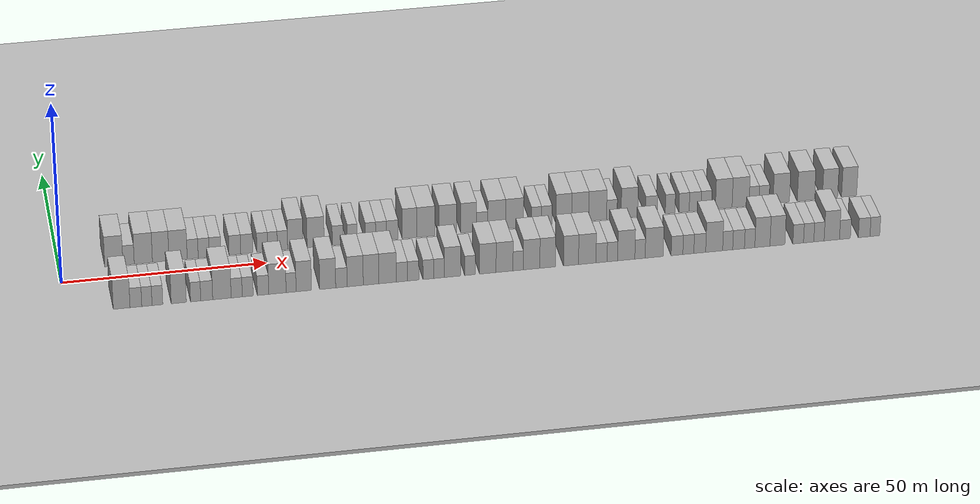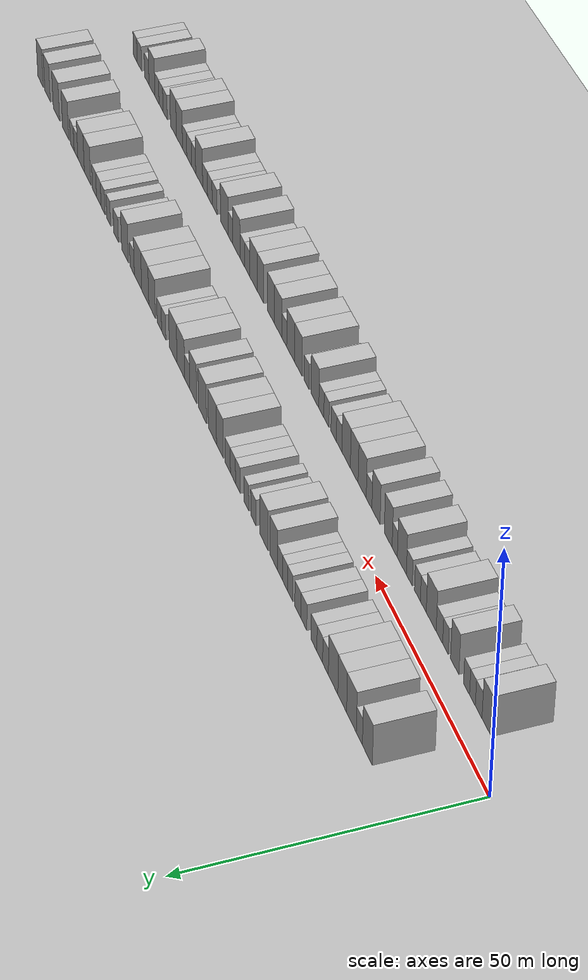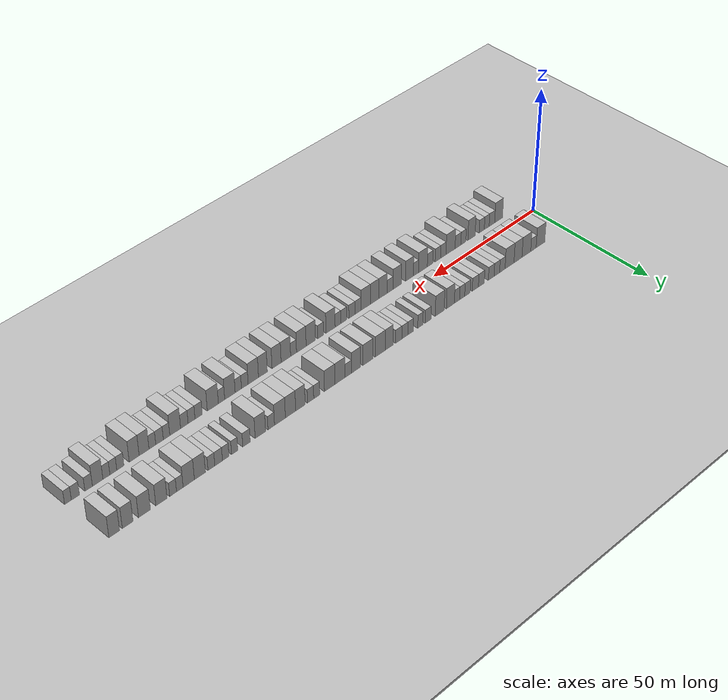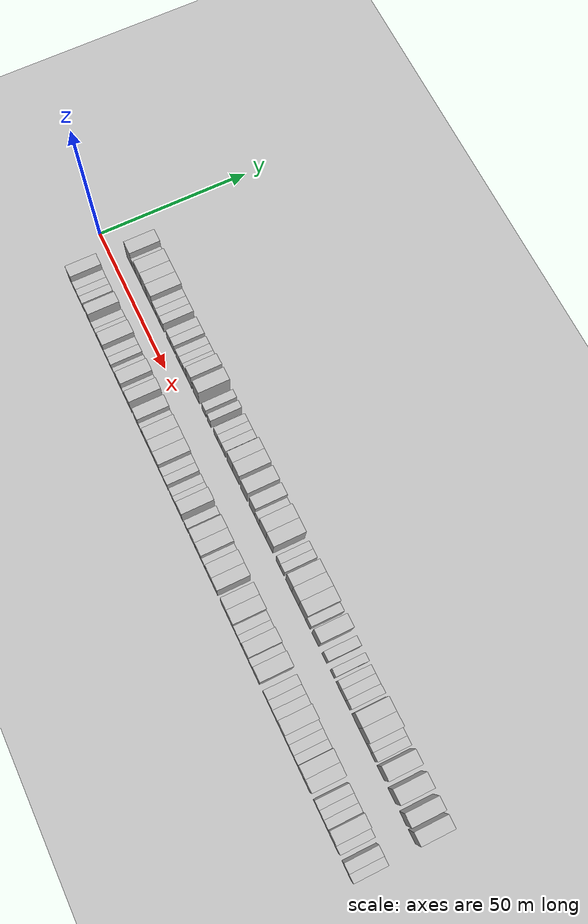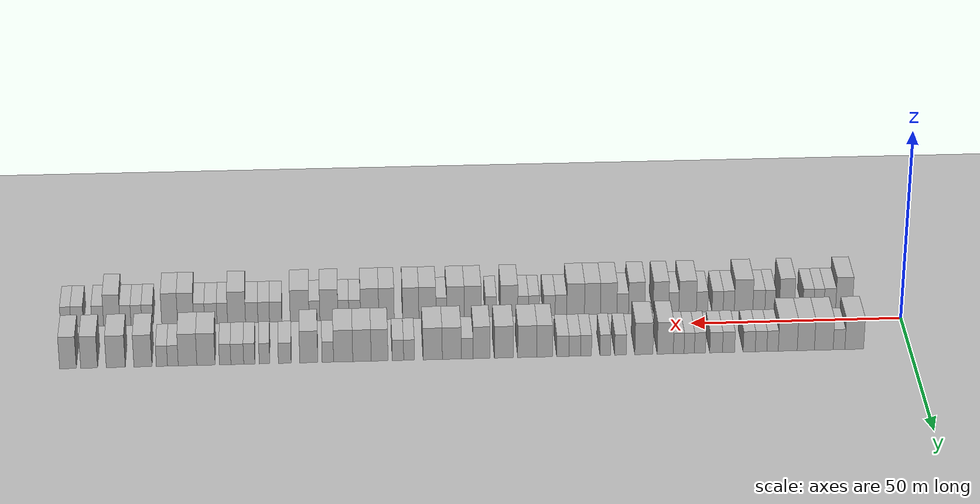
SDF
<?xml version="1.0" encoding="utf-8"?>

<sdf version="1.6">

   <world name="default">

      <gui fullscreen="0">

         <camera name="user_camera">

            <pose>-15 0 4.57585 0 0 0</pose>

            <view_controller>orbit</view_controller>

         </camera>

      </gui>

      <scene>

         <sky>

           <clouds>

             <speed>12</speed>

           </clouds>

         </sky>

         <ambient>0.4 0.4 0.4 1</ambient>

         <background>0.7 0.7 0.7 1</background>

         <shadows>1</shadows>

      </scene>

      <gravity>0 0 -9.8066</gravity>

      <magnetic_field>6e-06 2.3e-05 -4.2e-05</magnetic_field>

      <physics default="0" name="default_physics" type="ode">

         <ode>

            <solver>

               <type>quick</type>

               <iters>10</iters>

               <sor>1.0</sor>

               <use_dynamic_moi_rescaling>0</use_dynamic_moi_rescaling>

            </solver>

            <constraints>

               <cfm>0</cfm>

               <erp>0.2</erp>

               <contact_max_correcting_vel>100</contact_max_correcting_vel>

               <contact_surface_layer>0.001</contact_surface_layer>

            </constraints>

         </ode>

         <max_step_size>0.004</max_step_size>

         <real_time_factor>1</real_time_factor>

         <real_time_update_rate>250</real_time_update_rate>

      </physics>

      <light name="sun" type="directional">

         <cast_shadows>1</cast_shadows>

         <pose>0 0 10 0 0 0</pose>

         <diffuse>0.8 0.8 0.8 1</diffuse>

         <specular>0.2 0.2 0.2 1</specular>

         <attenuation>

            <range>1000</range>

            <constant>0.9</constant>

            <linear>0.01</linear>

            <quadratic>0.001</quadratic>

         </attenuation>

         <direction>-0.5 0.1 -0.9</direction>

      </light>

      <include>

         <name>ground_plane_1</name>

         <uri>model://HANNAS_ground_plane</uri>

         <pose>0 0 0  0 0 0</pose>

      </include>

      <include>

         <name>ground_plane_2</name>

         <uri>model://HANNAS_ground_plane</uri>

         <pose>100 0 0  0 0 0</pose>

      </include>

      <model name="building_1">

         <static>1</static>

         <pose frame="">13.2081 9.5000 0 0.000000 0.000000 1.570796</pose>

         <link name="link">

            <pose frame="">0 0 4.50 0 0 0</pose>

            <collision name="collision">

               <geometry>

                  <box>

                     <size>10.0000 4.4162 9.0000</size>

                  </box>

               </geometry>

               <max_contacts>10</max_contacts>

               <surface>

                  <contact>

                     <ode/>

                  </contact>

                  <bounce/>

                  <friction>

                     <torsional>

                        <ode/>

                     </torsional>

                     <ode/>

                  </friction>

               </surface>

            </collision>

            <visual name="visual">

               <cast_shadows>0</cast_shadows>

               <geometry>

                  <box>

                     <size>10.0000 4.4162 9.0000</size>

                  </box>

               </geometry>

               <material>

                  <script>

                     <uri>model://HANNAS_wall/materials/scripts</uri>

                     <uri>model://HANNAS_wall/materials/textures</uri>

                     <name>vrc/HANNAS_wall</name>

                  </script>

               </material>

            </visual>

            <self_collide>0</self_collide>

            <enable_wind>0</enable_wind>

            <kinematic>0</kinematic>

         </link>

      </model>

      <model name="building_2">

         <static>1</static>

         <pose frame="">16.7912 9.5000 0 0.000000 0.000000 1.570796</pose>

         <link name="link">

            <pose frame="">0 0 3.00 0 0 0</pose>

            <collision name="collision">

               <geometry>

                  <box>

                     <size>10.0000 2.7499 6.0000</size>

                  </box>

               </geometry>

               <max_contacts>10</max_contacts>

               <surface>

                  <contact>

                     <ode/>

                  </contact>

                  <bounce/>

                  <friction>

                     <torsional>

                        <ode/>

                     </torsional>

                     <ode/>

                  </friction>

               </surface>

            </collision>

            <visual name="visual">

               <cast_shadows>0</cast_shadows>

               <geometry>

                  <box>

                     <size>10.0000 2.7499 6.0000</size>

                  </box>

               </geometry>

               <material>

                  <script>

                     <uri>model://HANNAS_wall/materials/scripts</uri>

                     <uri>model://HANNAS_wall/materials/textures</uri>

                     <name>vrc/HANNAS_wall</name>

                  </script>

               </material>

            </visual>

            <self_collide>0</self_collide>

            <enable_wind>0</enable_wind>

            <kinematic>0</kinematic>

         </link>

      </model>

      <model name="building_3">

         <static>1</static>

         <pose frame="">20.3787 9.5000 0 0.000000 0.000000 1.570796</pose>

         <link name="link">

            <pose frame="">0 0 4.50 0 0 0</pose>

            <collision name="collision">

               <geometry>

                  <box>

                     <size>10.0000 4.4251 9.0000</size>

                  </box>

               </geometry>

               <max_contacts>10</max_contacts>

               <surface>

                  <contact>

                     <ode/>

                  </contact>

                  <bounce/>

                  <friction>

                     <torsional>

                        <ode/>

                     </torsional>

                     <ode/>

                  </friction>

               </surface>

            </collision>

            <visual name="visual">

               <cast_shadows>0</cast_shadows>

               <geometry>

                  <box>

                     <size>10.0000 4.4251 9.0000</size>

                  </box>

               </geometry>

               <material>

                  <script>

                     <uri>model://HANNAS_wall/materials/scripts</uri>

                     <uri>model://HANNAS_wall/materials/textures</uri>

                     <name>vrc/HANNAS_wall</name>

                  </script>

               </material>

            </visual>

            <self_collide>0</self_collide>

            <enable_wind>0</enable_wind>

            <kinematic>0</kinematic>

         </link>

      </model>

      <model name="building_4">

         <static>1</static>

         <pose frame="">24.6089 9.5000 0 0.000000 0.000000 1.570796</pose>

         <link name="link">

            <pose frame="">0 0 4.50 0 0 0</pose>

            <collision name="collision">

               <geometry>

                  <box>

                     <size>10.0000 4.0352 9.0000</size>

                  </box>

               </geometry>

               <max_contacts>10</max_contacts>

               <surface>

                  <contact>

                     <ode/>

                  </contact>

                  <bounce/>

                  <friction>

                     <torsional>

                        <ode/>

                     </torsional>

                     <ode/>

                  </friction>

               </surface>

            </collision>

            <visual name="visual">

               <cast_shadows>0</cast_shadows>

               <geometry>

                  <box>

                     <size>10.0000 4.0352 9.0000</size>

                  </box>

               </geometry>

               <material>

                  <script>

                     <uri>model://HANNAS_wall/materials/scripts</uri>

                     <uri>model://HANNAS_wall/materials/textures</uri>

                     <name>vrc/HANNAS_wall</name>

                  </script>

               </material>

            </visual>

            <self_collide>0</self_collide>

            <enable_wind>0</enable_wind>

            <kinematic>0</kinematic>

         </link>

      </model>

      <model name="building_5">

         <static>1</static>

         <pose frame="">28.8505 9.5000 0 0.000000 0.000000 1.570796</pose>

         <link name="link">

            <pose frame="">0 0 4.50 0 0 0</pose>

            <collision name="collision">

               <geometry>

                  <box>

                     <size>10.0000 4.4482 9.0000</size>

                  </box>

               </geometry>

               <max_contacts>10</max_contacts>

               <surface>

                  <contact>

                     <ode/>

                  </contact>

                  <bounce/>

                  <friction>

                     <torsional>

                        <ode/>

                     </torsional>

                     <ode/>

                  </friction>

               </surface>

            </collision>

            <visual name="visual">

               <cast_shadows>0</cast_shadows>

               <geometry>

                  <box>

                     <size>10.0000 4.4482 9.0000</size>

                  </box>

               </geometry>

               <material>

                  <script>

                     <uri>model://HANNAS_wall/materials/scripts</uri>

                     <uri>model://HANNAS_wall/materials/textures</uri>

                     <name>vrc/HANNAS_wall</name>

                  </script>

               </material>

            </visual>

            <self_collide>0</self_collide>

            <enable_wind>0</enable_wind>

            <kinematic>0</kinematic>

         </link>

      </model>

      <model name="building_6">

         <static>1</static>

         <pose frame="">32.4197 9.5000 0 0.000000 0.000000 1.570796</pose>

         <link name="link">

            <pose frame="">0 0 3.00 0 0 0</pose>

            <collision name="collision">

               <geometry>

                  <box>

                     <size>10.0000 2.6902 6.0000</size>

                  </box>

               </geometry>

               <max_contacts>10</max_contacts>

               <surface>

                  <contact>

                     <ode/>

                  </contact>

                  <bounce/>

                  <friction>

                     <torsional>

                        <ode/>

                     </torsional>

                     <ode/>

                  </friction>

               </surface>

            </collision>

            <visual name="visual">

               <cast_shadows>0</cast_shadows>

               <geometry>

                  <box>

                     <size>10.0000 2.6902 6.0000</size>

                  </box>

               </geometry>

               <material>

                  <script>

                     <uri>model://HANNAS_wall/materials/scripts</uri>

                     <uri>model://HANNAS_wall/materials/textures</uri>

                     <name>vrc/HANNAS_wall</name>

                  </script>

               </material>

            </visual>

            <self_collide>0</self_collide>

            <enable_wind>0</enable_wind>

            <kinematic>0</kinematic>

         </link>

      </model>

      <model name="building_7">

         <static>1</static>

         <pose frame="">35.1305 9.5000 0 0.000000 0.000000 1.570796</pose>

         <link name="link">

            <pose frame="">0 0 3.00 0 0 0</pose>

            <collision name="collision">

               <geometry>

                  <box>

                     <size>10.0000 2.7314 6.0000</size>

                  </box>

               </geometry>

               <max_contacts>10</max_contacts>

               <surface>

                  <contact>

                     <ode/>

                  </contact>

                  <bounce/>

                  <friction>

                     <torsional>

                        <ode/>

                     </torsional>

                     <ode/>

                  </friction>

               </surface>

            </collision>

            <visual name="visual">

               <cast_shadows>0</cast_shadows>

               <geometry>

                  <box>

                     <size>10.0000 2.7314 6.0000</size>

                  </box>

               </geometry>

               <material>

                  <script>

                     <uri>model://HANNAS_wall/materials/scripts</uri>

                     <uri>model://HANNAS_wall/materials/textures</uri>

                     <name>vrc/HANNAS_wall</name>

                  </script>

               </material>

            </visual>

            <self_collide>0</self_collide>

            <enable_wind>0</enable_wind>

            <kinematic>0</kinematic>

         </link>

      </model>

      <model name="building_8">

         <static>1</static>

         <pose frame="">37.9028 9.5000 0 0.000000 0.000000 1.570796</pose>

         <link name="link">

            <pose frame="">0 0 3.00 0 0 0</pose>

            <collision name="collision">

               <geometry>

                  <box>

                     <size>10.0000 2.8131 6.0000</size>

                  </box>

               </geometry>

               <max_contacts>10</max_contacts>

               <surface>

                  <contact>

                     <ode/>

                  </contact>

                  <bounce/>

                  <friction>

                     <torsional>

                        <ode/>

                     </torsional>

                     <ode/>

                  </friction>

               </surface>

            </collision>

            <visual name="visual">

               <cast_shadows>0</cast_shadows>

               <geometry>

                  <box>

                     <size>10.0000 2.8131 6.0000</size>

                  </box>

               </geometry>

               <material>

                  <script>

                     <uri>model://HANNAS_wall/materials/scripts</uri>

                     <uri>model://HANNAS_wall/materials/textures</uri>

                     <name>vrc/HANNAS_wall</name>

                  </script>

               </material>

            </visual>

            <self_collide>0</self_collide>

            <enable_wind>0</enable_wind>

            <kinematic>0</kinematic>

         </link>

      </model>

      <model name="building_9">

         <static>1</static>

         <pose frame="">42.7395 9.5000 0 0.000000 0.000000 1.570796</pose>

         <link name="link">

            <pose frame="">0 0 3.00 0 0 0</pose>

            <collision name="collision">

               <geometry>

                  <box>

                     <size>10.0000 2.8603 6.0000</size>

                  </box>

               </geometry>

               <max_contacts>10</max_contacts>

               <surface>

                  <contact>

                     <ode/>

                  </contact>

                  <bounce/>

                  <friction>

                     <torsional>

                        <ode/>

                     </torsional>

                     <ode/>

                  </friction>

               </surface>

            </collision>

            <visual name="visual">

               <cast_shadows>0</cast_shadows>

               <geometry>

                  <box>

                     <size>10.0000 2.8603 6.0000</size>

                  </box>

               </geometry>

               <material>

                  <script>

                     <uri>model://HANNAS_wall/materials/scripts</uri>

                     <uri>model://HANNAS_wall/materials/textures</uri>

                     <name>vrc/HANNAS_wall</name>

                  </script>

               </material>

            </visual>

            <self_collide>0</self_collide>

            <enable_wind>0</enable_wind>

            <kinematic>0</kinematic>

         </link>

      </model>

      <model name="building_10">

         <static>1</static>

         <pose frame="">45.6591 9.5000 0 0.000000 0.000000 1.570796</pose>

         <link name="link">

            <pose frame="">0 0 3.00 0 0 0</pose>

            <collision name="collision">

               <geometry>

                  <box>

                     <size>10.0000 2.9788 6.0000</size>

                  </box>

               </geometry>

               <max_contacts>10</max_contacts>

               <surface>

                  <contact>

                     <ode/>

                  </contact>

                  <bounce/>

                  <friction>

                     <torsional>

                        <ode/>

                     </torsional>

                     <ode/>

                  </friction>

               </surface>

            </collision>

            <visual name="visual">

               <cast_shadows>0</cast_shadows>

               <geometry>

                  <box>

                     <size>10.0000 2.9788 6.0000</size>

                  </box>

               </geometry>

               <material>

                  <script>

                     <uri>model://HANNAS_wall/materials/scripts</uri>

                     <uri>model://HANNAS_wall/materials/textures</uri>

                     <name>vrc/HANNAS_wall</name>

                  </script>

               </material>

            </visual>

            <self_collide>0</self_collide>

            <enable_wind>0</enable_wind>

            <kinematic>0</kinematic>

         </link>

      </model>

      <model name="building_11">

         <static>1</static>

         <pose frame="">49.4568 9.5000 0 0.000000 0.000000 1.570796</pose>

         <link name="link">

            <pose frame="">0 0 3.00 0 0 0</pose>

            <collision name="collision">

               <geometry>

                  <box>

                     <size>10.0000 2.6166 6.0000</size>

                  </box>

               </geometry>

               <max_contacts>10</max_contacts>

               <surface>

                  <contact>

                     <ode/>

                  </contact>

                  <bounce/>

                  <friction>

                     <torsional>

                        <ode/>

                     </torsional>

                     <ode/>

                  </friction>

               </surface>

            </collision>

            <visual name="visual">

               <cast_shadows>0</cast_shadows>

               <geometry>

                  <box>

                     <size>10.0000 2.6166 6.0000</size>

                  </box>

               </geometry>

               <material>

                  <script>

                     <uri>model://HANNAS_wall/materials/scripts</uri>

                     <uri>model://HANNAS_wall/materials/textures</uri>

                     <name>vrc/HANNAS_wall</name>

                  </script>

               </material>

            </visual>

            <self_collide>0</self_collide>

            <enable_wind>0</enable_wind>

            <kinematic>0</kinematic>

         </link>

      </model>

      <model name="building_12">

         <static>1</static>

         <pose frame="">51.9722 9.5000 0 0.000000 0.000000 1.570796</pose>

         <link name="link">

            <pose frame="">0 0 3.00 0 0 0</pose>

            <collision name="collision">

               <geometry>

                  <box>

                     <size>10.0000 2.4142 6.0000</size>

                  </box>

               </geometry>

               <max_contacts>10</max_contacts>

               <surface>

                  <contact>

                     <ode/>

                  </contact>

                  <bounce/>

                  <friction>

                     <torsional>

                        <ode/>

                     </torsional>

                     <ode/>

                  </friction>

               </surface>

            </collision>

            <visual name="visual">

               <cast_shadows>0</cast_shadows>

               <geometry>

                  <box>

                     <size>10.0000 2.4142 6.0000</size>

                  </box>

               </geometry>

               <material>

                  <script>

                     <uri>model://HANNAS_wall/materials/scripts</uri>

                     <uri>model://HANNAS_wall/materials/textures</uri>

                     <name>vrc/HANNAS_wall</name>

                  </script>

               </material>

            </visual>

            <self_collide>0</self_collide>

            <enable_wind>0</enable_wind>

            <kinematic>0</kinematic>

         </link>

      </model>

      <model name="building_13">

         <static>1</static>

         <pose frame="">54.4409 9.5000 0 0.000000 0.000000 1.570796</pose>

         <link name="link">

            <pose frame="">0 0 3.00 0 0 0</pose>

            <collision name="collision">

               <geometry>

                  <box>

                     <size>10.0000 2.5232 6.0000</size>

                  </box>

               </geometry>

               <max_contacts>10</max_contacts>

               <surface>

                  <contact>

                     <ode/>

                  </contact>

                  <bounce/>

                  <friction>

                     <torsional>

                        <ode/>

                     </torsional>

                     <ode/>

                  </friction>

               </surface>

            </collision>

            <visual name="visual">

               <cast_shadows>0</cast_shadows>

               <geometry>

                  <box>

                     <size>10.0000 2.5232 6.0000</size>

                  </box>

               </geometry>

               <material>

                  <script>

                     <uri>model://HANNAS_wall/materials/scripts</uri>

                     <uri>model://HANNAS_wall/materials/textures</uri>

                     <name>vrc/HANNAS_wall</name>

                  </script>

               </material>

            </visual>

            <self_collide>0</self_collide>

            <enable_wind>0</enable_wind>

            <kinematic>0</kinematic>

         </link>

      </model>

      <model name="building_14">

         <static>1</static>

         <pose frame="">57.5914 9.5000 0 0.000000 0.000000 1.570796</pose>

         <link name="link">

            <pose frame="">0 0 4.50 0 0 0</pose>

            <collision name="collision">

               <geometry>

                  <box>

                     <size>10.0000 3.7779 9.0000</size>

                  </box>

               </geometry>

               <max_contacts>10</max_contacts>

               <surface>

                  <contact>

                     <ode/>

                  </contact>

                  <bounce/>

                  <friction>

                     <torsional>

                        <ode/>

                     </torsional>

                     <ode/>

                  </friction>

               </surface>

            </collision>

            <visual name="visual">

               <cast_shadows>0</cast_shadows>

               <geometry>

                  <box>

                     <size>10.0000 3.7779 9.0000</size>

                  </box>

               </geometry>

               <material>

                  <script>

                     <uri>model://HANNAS_wall/materials/scripts</uri>

                     <uri>model://HANNAS_wall/materials/textures</uri>

                     <name>vrc/HANNAS_wall</name>

                  </script>

               </material>

            </visual>

            <self_collide>0</self_collide>

            <enable_wind>0</enable_wind>

            <kinematic>0</kinematic>

         </link>

      </model>

      <model name="building_15">

         <static>1</static>

         <pose frame="">62.5918 9.5000 0 0.000000 0.000000 1.570796</pose>

         <link name="link">

            <pose frame="">0 0 4.50 0 0 0</pose>

            <collision name="collision">

               <geometry>

                  <box>

                     <size>10.0000 4.2228 9.0000</size>

                  </box>

               </geometry>

               <max_contacts>10</max_contacts>

               <surface>

                  <contact>

                     <ode/>

                  </contact>

                  <bounce/>

                  <friction>

                     <torsional>

                        <ode/>

                     </torsional>

                     <ode/>

                  </friction>

               </surface>

            </collision>

            <visual name="visual">

               <cast_shadows>0</cast_shadows>

               <geometry>

                  <box>

                     <size>10.0000 4.2228 9.0000</size>

                  </box>

               </geometry>

               <material>

                  <script>

                     <uri>model://HANNAS_wall/materials/scripts</uri>

                     <uri>model://HANNAS_wall/materials/textures</uri>

                     <name>vrc/HANNAS_wall</name>

                  </script>

               </material>

            </visual>

            <self_collide>0</self_collide>

            <enable_wind>0</enable_wind>

            <kinematic>0</kinematic>

         </link>

      </model>

      <model name="building_16">

         <static>1</static>

         <pose frame="">68.0669 9.5000 0 0.000000 0.000000 1.570796</pose>

         <link name="link">

            <pose frame="">0 0 3.00 0 0 0</pose>

            <collision name="collision">

               <geometry>

                  <box>

                     <size>10.0000 2.7273 6.0000</size>

                  </box>

               </geometry>

               <max_contacts>10</max_contacts>

               <surface>

                  <contact>

                     <ode/>

                  </contact>

                  <bounce/>

                  <friction>

                     <torsional>

                        <ode/>

                     </torsional>

                     <ode/>

                  </friction>

               </surface>

            </collision>

            <visual name="visual">

               <cast_shadows>0</cast_shadows>

               <geometry>

                  <box>

                     <size>10.0000 2.7273 6.0000</size>

                  </box>

               </geometry>

               <material>

                  <script>

                     <uri>model://HANNAS_wall/materials/scripts</uri>

                     <uri>model://HANNAS_wall/materials/textures</uri>

                     <name>vrc/HANNAS_wall</name>

                  </script>

               </material>

            </visual>

            <self_collide>0</self_collide>

            <enable_wind>0</enable_wind>

            <kinematic>0</kinematic>

         </link>

      </model>

      <model name="building_17">

         <static>1</static>

         <pose frame="">71.6421 9.5000 0 0.000000 0.000000 1.570796</pose>

         <link name="link">

            <pose frame="">0 0 3.00 0 0 0</pose>

            <collision name="collision">

               <geometry>

                  <box>

                     <size>10.0000 2.4231 6.0000</size>

                  </box>

               </geometry>

               <max_contacts>10</max_contacts>

               <surface>

                  <contact>

                     <ode/>

                  </contact>

                  <bounce/>

                  <friction>

                     <torsional>

                        <ode/>

                     </torsional>

                     <ode/>

                  </friction>

               </surface>

            </collision>

            <visual name="visual">

               <cast_shadows>0</cast_shadows>

               <geometry>

                  <box>

                     <size>10.0000 2.4231 6.0000</size>

                  </box>

               </geometry>

               <material>

                  <script>

                     <uri>model://HANNAS_wall/materials/scripts</uri>

                     <uri>model://HANNAS_wall/materials/textures</uri>

                     <name>vrc/HANNAS_wall</name>

                  </script>

               </material>

            </visual>

            <self_collide>0</self_collide>

            <enable_wind>0</enable_wind>

            <kinematic>0</kinematic>

         </link>

      </model>

      <model name="building_18">

         <static>1</static>

         <pose frame="">76.1286 9.5000 0 0.000000 0.000000 1.570796</pose>

         <link name="link">

            <pose frame="">0 0 3.00 0 0 0</pose>

            <collision name="collision">

               <geometry>

                  <box>

                     <size>10.0000 2.5498 6.0000</size>

                  </box>

               </geometry>

               <max_contacts>10</max_contacts>

               <surface>

                  <contact>

                     <ode/>

                  </contact>

                  <bounce/>

                  <friction>

                     <torsional>

                        <ode/>

                     </torsional>

                     <ode/>

                  </friction>

               </surface>

            </collision>

            <visual name="visual">

               <cast_shadows>0</cast_shadows>

               <geometry>

                  <box>

                     <size>10.0000 2.5498 6.0000</size>

                  </box>

               </geometry>

               <material>

                  <script>

                     <uri>model://HANNAS_wall/materials/scripts</uri>

                     <uri>model://HANNAS_wall/materials/textures</uri>

                     <name>vrc/HANNAS_wall</name>

                  </script>

               </material>

            </visual>

            <self_collide>0</self_collide>

            <enable_wind>0</enable_wind>

            <kinematic>0</kinematic>

         </link>

      </model>

      <model name="building_19">

         <static>1</static>

         <pose frame="">78.7654 9.5000 0 0.000000 0.000000 1.570796</pose>

         <link name="link">

            <pose frame="">0 0 3.00 0 0 0</pose>

            <collision name="collision">

               <geometry>

                  <box>

                     <size>10.0000 2.7238 6.0000</size>

                  </box>

               </geometry>

               <max_contacts>10</max_contacts>

               <surface>

                  <contact>

                     <ode/>

                  </contact>

                  <bounce/>

                  <friction>

                     <torsional>

                        <ode/>

                     </torsional>

                     <ode/>

                  </friction>

               </surface>

            </collision>

            <visual name="visual">

               <cast_shadows>0</cast_shadows>

               <geometry>

                  <box>

                     <size>10.0000 2.7238 6.0000</size>

                  </box>

               </geometry>

               <material>

                  <script>

                     <uri>model://HANNAS_wall/materials/scripts</uri>

                     <uri>model://HANNAS_wall/materials/textures</uri>

                     <name>vrc/HANNAS_wall</name>

                  </script>

               </material>

            </visual>

            <self_collide>0</self_collide>

            <enable_wind>0</enable_wind>

            <kinematic>0</kinematic>

         </link>

      </model>

      <model name="building_20">

         <static>1</static>

         <pose frame="">81.5579 9.5000 0 0.000000 0.000000 1.570796</pose>

         <link name="link">

            <pose frame="">0 0 3.00 0 0 0</pose>

            <collision name="collision">

               <geometry>

                  <box>

                     <size>10.0000 2.8613 6.0000</size>

                  </box>

               </geometry>

               <max_contacts>10</max_contacts>

               <surface>

                  <contact>

                     <ode/>

                  </contact>

                  <bounce/>

                  <friction>

                     <torsional>

                        <ode/>

                     </torsional>

                     <ode/>

                  </friction>

               </surface>

            </collision>

            <visual name="visual">

               <cast_shadows>0</cast_shadows>

               <geometry>

                  <box>

                     <size>10.0000 2.8613 6.0000</size>

                  </box>

               </geometry>

               <material>

                  <script>

                     <uri>model://HANNAS_wall/materials/scripts</uri>

                     <uri>model://HANNAS_wall/materials/textures</uri>

                     <name>vrc/HANNAS_wall</name>

                  </script>

               </material>

            </visual>

            <self_collide>0</self_collide>

            <enable_wind>0</enable_wind>

            <kinematic>0</kinematic>

         </link>

      </model>

      <model name="building_21">

         <static>1</static>

         <pose frame="">85.8065 9.5000 0 0.000000 0.000000 1.570796</pose>

         <link name="link">

            <pose frame="">0 0 4.50 0 0 0</pose>

            <collision name="collision">

               <geometry>

                  <box>

                     <size>10.0000 3.6358 9.0000</size>

                  </box>

               </geometry>

               <max_contacts>10</max_contacts>

               <surface>

                  <contact>

                     <ode/>

                  </contact>

                  <bounce/>

                  <friction>

                     <torsional>

                        <ode/>

                     </torsional>

                     <ode/>

                  </friction>

               </surface>

            </collision>

            <visual name="visual">

               <cast_shadows>0</cast_shadows>

               <geometry>

                  <box>

                     <size>10.0000 3.6358 9.0000</size>

                  </box>

               </geometry>

               <material>

                  <script>

                     <uri>model://HANNAS_wall/materials/scripts</uri>

                     <uri>model://HANNAS_wall/materials/textures</uri>

                     <name>vrc/HANNAS_wall</name>

                  </script>

               </material>

            </visual>

            <self_collide>0</self_collide>

            <enable_wind>0</enable_wind>

            <kinematic>0</kinematic>

         </link>

      </model>

      <model name="building_22">

         <static>1</static>

         <pose frame="">89.8569 9.5000 0 0.000000 0.000000 1.570796</pose>

         <link name="link">

            <pose frame="">0 0 4.50 0 0 0</pose>

            <collision name="collision">

               <geometry>

                  <box>

                     <size>10.0000 4.4651 9.0000</size>

                  </box>

               </geometry>

               <max_contacts>10</max_contacts>

               <surface>

                  <contact>

                     <ode/>

                  </contact>

                  <bounce/>

                  <friction>

                     <torsional>

                        <ode/>

                     </torsional>

                     <ode/>

                  </friction>

               </surface>

            </collision>

            <visual name="visual">

               <cast_shadows>0</cast_shadows>

               <geometry>

                  <box>

                     <size>10.0000 4.4651 9.0000</size>

                  </box>

               </geometry>

               <material>

                  <script>

                     <uri>model://HANNAS_wall/materials/scripts</uri>

                     <uri>model://HANNAS_wall/materials/textures</uri>

                     <name>vrc/HANNAS_wall</name>

                  </script>

               </material>

            </visual>

            <self_collide>0</self_collide>

            <enable_wind>0</enable_wind>

            <kinematic>0</kinematic>

         </link>

      </model>

      <model name="building_23">

         <static>1</static>

         <pose frame="">95.3158 9.5000 0 0.000000 0.000000 1.570796</pose>

         <link name="link">

            <pose frame="">0 0 4.50 0 0 0</pose>

            <collision name="collision">

               <geometry>

                  <box>

                     <size>10.0000 4.4527 9.0000</size>

                  </box>

               </geometry>

               <max_contacts>10</max_contacts>

               <surface>

                  <contact>

                     <ode/>

                  </contact>

                  <bounce/>

                  <friction>

                     <torsional>

                        <ode/>

                     </torsional>

                     <ode/>

                  </friction>

               </surface>

            </collision>

            <visual name="visual">

               <cast_shadows>0</cast_shadows>

               <geometry>

                  <box>

                     <size>10.0000 4.4527 9.0000</size>

                  </box>

               </geometry>

               <material>

                  <script>

                     <uri>model://HANNAS_wall/materials/scripts</uri>

                     <uri>model://HANNAS_wall/materials/textures</uri>

                     <name>vrc/HANNAS_wall</name>

                  </script>

               </material>

            </visual>

            <self_collide>0</self_collide>

            <enable_wind>0</enable_wind>

            <kinematic>0</kinematic>

         </link>

      </model>

      <model name="building_24">

         <static>1</static>

         <pose frame="">100.5051 9.5000 0 0.000000 0.000000 1.570796</pose>

         <link name="link">

            <pose frame="">0 0 4.50 0 0 0</pose>

            <collision name="collision">

               <geometry>

                  <box>

                     <size>10.0000 3.9260 9.0000</size>

                  </box>

               </geometry>

               <max_contacts>10</max_contacts>

               <surface>

                  <contact>

                     <ode/>

                  </contact>

                  <bounce/>

                  <friction>

                     <torsional>

                        <ode/>

                     </torsional>

                     <ode/>

                  </friction>

               </surface>

            </collision>

            <visual name="visual">

               <cast_shadows>0</cast_shadows>

               <geometry>

                  <box>

                     <size>10.0000 3.9260 9.0000</size>

                  </box>

               </geometry>

               <material>

                  <script>

                     <uri>model://HANNAS_wall/materials/scripts</uri>

                     <uri>model://HANNAS_wall/materials/textures</uri>

                     <name>vrc/HANNAS_wall</name>

                  </script>

               </material>

            </visual>

            <self_collide>0</self_collide>

            <enable_wind>0</enable_wind>

            <kinematic>0</kinematic>

         </link>

      </model>

      <model name="building_25">

         <static>1</static>

         <pose frame="">103.8729 9.5000 0 0.000000 0.000000 1.570796</pose>

         <link name="link">

            <pose frame="">0 0 3.00 0 0 0</pose>

            <collision name="collision">

               <geometry>

                  <box>

                     <size>10.0000 2.8097 6.0000</size>

                  </box>

               </geometry>

               <max_contacts>10</max_contacts>

               <surface>

                  <contact>

                     <ode/>

                  </contact>

                  <bounce/>

                  <friction>

                     <torsional>

                        <ode/>

                     </torsional>

                     <ode/>

                  </friction>

               </surface>

            </collision>

            <visual name="visual">

               <cast_shadows>0</cast_shadows>

               <geometry>

                  <box>

                     <size>10.0000 2.8097 6.0000</size>

                  </box>

               </geometry>

               <material>

                  <script>

                     <uri>model://HANNAS_wall/materials/scripts</uri>

                     <uri>model://HANNAS_wall/materials/textures</uri>

                     <name>vrc/HANNAS_wall</name>

                  </script>

               </material>

            </visual>

            <self_collide>0</self_collide>

            <enable_wind>0</enable_wind>

            <kinematic>0</kinematic>

         </link>

      </model>

      <model name="building_26">

         <static>1</static>

         <pose frame="">107.4853 9.5000 0 0.000000 0.000000 1.570796</pose>

         <link name="link">

            <pose frame="">0 0 4.50 0 0 0</pose>

            <collision name="collision">

               <geometry>

                  <box>

                     <size>10.0000 4.4151 9.0000</size>

                  </box>

               </geometry>

               <max_contacts>10</max_contacts>

               <surface>

                  <contact>

                     <ode/>

                  </contact>

                  <bounce/>

                  <friction>

                     <torsional>

                        <ode/>

                     </torsional>

                     <ode/>

                  </friction>

               </surface>

            </collision>

            <visual name="visual">

               <cast_shadows>0</cast_shadows>

               <geometry>

                  <box>

                     <size>10.0000 4.4151 9.0000</size>

                  </box>

               </geometry>

               <material>

                  <script>

                     <uri>model://HANNAS_wall/materials/scripts</uri>

                     <uri>model://HANNAS_wall/materials/textures</uri>

                     <name>vrc/HANNAS_wall</name>

                  </script>

               </material>

            </visual>

            <self_collide>0</self_collide>

            <enable_wind>0</enable_wind>

            <kinematic>0</kinematic>

         </link>

      </model>

      <model name="building_27">

         <static>1</static>

         <pose frame="">111.9275 9.5000 0 0.000000 0.000000 1.570796</pose>

         <link name="link">

            <pose frame="">0 0 4.50 0 0 0</pose>

            <collision name="collision">

               <geometry>

                  <box>

                     <size>10.0000 4.4693 9.0000</size>

                  </box>

               </geometry>

               <max_contacts>10</max_contacts>

               <surface>

                  <contact>

                     <ode/>

                  </contact>

                  <bounce/>

                  <friction>

                     <torsional>

                        <ode/>

                     </torsional>

                     <ode/>

                  </friction>

               </surface>

            </collision>

            <visual name="visual">

               <cast_shadows>0</cast_shadows>

               <geometry>

                  <box>

                     <size>10.0000 4.4693 9.0000</size>

                  </box>

               </geometry>

               <material>

                  <script>

                     <uri>model://HANNAS_wall/materials/scripts</uri>

                     <uri>model://HANNAS_wall/materials/textures</uri>

                     <name>vrc/HANNAS_wall</name>

                  </script>

               </material>

            </visual>

            <self_collide>0</self_collide>

            <enable_wind>0</enable_wind>

            <kinematic>0</kinematic>

         </link>

      </model>

      <model name="building_28">

         <static>1</static>

         <pose frame="">117.4270 9.5000 0 0.000000 0.000000 1.570796</pose>

         <link name="link">

            <pose frame="">0 0 3.00 0 0 0</pose>

            <collision name="collision">

               <geometry>

                  <box>

                     <size>10.0000 2.5297 6.0000</size>

                  </box>

               </geometry>

               <max_contacts>10</max_contacts>

               <surface>

                  <contact>

                     <ode/>

                  </contact>

                  <bounce/>

                  <friction>

                     <torsional>

                        <ode/>

                     </torsional>

                     <ode/>

                  </friction>

               </surface>

            </collision>

            <visual name="visual">

               <cast_shadows>0</cast_shadows>

               <geometry>

                  <box>

                     <size>10.0000 2.5297 6.0000</size>

                  </box>

               </geometry>

               <material>

                  <script>

                     <uri>model://HANNAS_wall/materials/scripts</uri>

                     <uri>model://HANNAS_wall/materials/textures</uri>

                     <name>vrc/HANNAS_wall</name>

                  </script>

               </material>

            </visual>

            <self_collide>0</self_collide>

            <enable_wind>0</enable_wind>

            <kinematic>0</kinematic>

         </link>

      </model>

      <model name="building_29">

         <static>1</static>

         <pose frame="">120.0156 9.5000 0 0.000000 0.000000 1.570796</pose>

         <link name="link">

            <pose frame="">0 0 3.00 0 0 0</pose>

            <collision name="collision">

               <geometry>

                  <box>

                     <size>10.0000 2.6473 6.0000</size>

                  </box>

               </geometry>

               <max_contacts>10</max_contacts>

               <surface>

                  <contact>

                     <ode/>

                  </contact>

                  <bounce/>

                  <friction>

                     <torsional>

                        <ode/>

                     </torsional>

                     <ode/>

                  </friction>

               </surface>

            </collision>

            <visual name="visual">

               <cast_shadows>0</cast_shadows>

               <geometry>

                  <box>

                     <size>10.0000 2.6473 6.0000</size>

                  </box>

               </geometry>

               <material>

                  <script>

                     <uri>model://HANNAS_wall/materials/scripts</uri>

                     <uri>model://HANNAS_wall/materials/textures</uri>

                     <name>vrc/HANNAS_wall</name>

                  </script>

               </material>

            </visual>

            <self_collide>0</self_collide>

            <enable_wind>0</enable_wind>

            <kinematic>0</kinematic>

         </link>

      </model>

      <model name="building_30">

         <static>1</static>

         <pose frame="">124.3036 9.5000 0 0.000000 0.000000 1.570796</pose>

         <link name="link">

            <pose frame="">0 0 4.50 0 0 0</pose>

            <collision name="collision">

               <geometry>

                  <box>

                     <size>10.0000 3.9288 9.0000</size>

                  </box>

               </geometry>

               <max_contacts>10</max_contacts>

               <surface>

                  <contact>

                     <ode/>

                  </contact>

                  <bounce/>

                  <friction>

                     <torsional>

                        <ode/>

                     </torsional>

                     <ode/>

                  </friction>

               </surface>

            </collision>

            <visual name="visual">

               <cast_shadows>0</cast_shadows>

               <geometry>

                  <box>

                     <size>10.0000 3.9288 9.0000</size>

                  </box>

               </geometry>

               <material>

                  <script>

                     <uri>model://HANNAS_wall/materials/scripts</uri>

                     <uri>model://HANNAS_wall/materials/textures</uri>

                     <name>vrc/HANNAS_wall</name>

                  </script>

               </material>

            </visual>

            <self_collide>0</self_collide>

            <enable_wind>0</enable_wind>

            <kinematic>0</kinematic>

         </link>

      </model>

      <model name="building_31">

         <static>1</static>

         <pose frame="">128.4004 9.5000 0 0.000000 0.000000 1.570796</pose>

         <link name="link">

            <pose frame="">0 0 4.50 0 0 0</pose>

            <collision name="collision">

               <geometry>

                  <box>

                     <size>10.0000 4.2649 9.0000</size>

                  </box>

               </geometry>

               <max_contacts>10</max_contacts>

               <surface>

                  <contact>

                     <ode/>

                  </contact>

                  <bounce/>

                  <friction>

                     <torsional>

                        <ode/>

                     </torsional>

                     <ode/>

                  </friction>

               </surface>

            </collision>

            <visual name="visual">

               <cast_shadows>0</cast_shadows>

               <geometry>

                  <box>

                     <size>10.0000 4.2649 9.0000</size>

                  </box>

               </geometry>

               <material>

                  <script>

                     <uri>model://HANNAS_wall/materials/scripts</uri>

                     <uri>model://HANNAS_wall/materials/textures</uri>

                     <name>vrc/HANNAS_wall</name>

                  </script>

               </material>

            </visual>

            <self_collide>0</self_collide>

            <enable_wind>0</enable_wind>

            <kinematic>0</kinematic>

         </link>

      </model>

      <model name="building_32">

         <static>1</static>

         <pose frame="">132.7663 9.5000 0 0.000000 0.000000 1.570796</pose>

         <link name="link">

            <pose frame="">0 0 4.50 0 0 0</pose>

            <collision name="collision">

               <geometry>

                  <box>

                     <size>10.0000 4.4671 9.0000</size>

                  </box>

               </geometry>

               <max_contacts>10</max_contacts>

               <surface>

                  <contact>

                     <ode/>

                  </contact>

                  <bounce/>

                  <friction>

                     <torsional>

                        <ode/>

                     </torsional>

                     <ode/>

                  </friction>

               </surface>

            </collision>

            <visual name="visual">

               <cast_shadows>0</cast_shadows>

               <geometry>

                  <box>

                     <size>10.0000 4.4671 9.0000</size>

                  </box>

               </geometry>

               <material>

                  <script>

                     <uri>model://HANNAS_wall/materials/scripts</uri>

                     <uri>model://HANNAS_wall/materials/textures</uri>

                     <name>vrc/HANNAS_wall</name>

                  </script>

               </material>

            </visual>

            <self_collide>0</self_collide>

            <enable_wind>0</enable_wind>

            <kinematic>0</kinematic>

         </link>

      </model>

      <model name="building_33">

         <static>1</static>

         <pose frame="">136.3278 9.5000 0 0.000000 0.000000 1.570796</pose>

         <link name="link">

            <pose frame="">0 0 3.00 0 0 0</pose>

            <collision name="collision">

               <geometry>

                  <box>

                     <size>10.0000 2.6558 6.0000</size>

                  </box>

               </geometry>

               <max_contacts>10</max_contacts>

               <surface>

                  <contact>

                     <ode/>

                  </contact>

                  <bounce/>

                  <friction>

                     <torsional>

                        <ode/>

                     </torsional>

                     <ode/>

                  </friction>

               </surface>

            </collision>

            <visual name="visual">

               <cast_shadows>0</cast_shadows>

               <geometry>

                  <box>

                     <size>10.0000 2.6558 6.0000</size>

                  </box>

               </geometry>

               <material>

                  <script>

                     <uri>model://HANNAS_wall/materials/scripts</uri>

                     <uri>model://HANNAS_wall/materials/textures</uri>

                     <name>vrc/HANNAS_wall</name>

                  </script>

               </material>

            </visual>

            <self_collide>0</self_collide>

            <enable_wind>0</enable_wind>

            <kinematic>0</kinematic>

         </link>

      </model>

      <model name="building_34">

         <static>1</static>

         <pose frame="">140.7529 9.5000 0 0.000000 0.000000 1.570796</pose>

         <link name="link">

            <pose frame="">0 0 4.50 0 0 0</pose>

            <collision name="collision">

               <geometry>

                  <box>

                     <size>10.0000 4.1943 9.0000</size>

                  </box>

               </geometry>

               <max_contacts>10</max_contacts>

               <surface>

                  <contact>

                     <ode/>

                  </contact>

                  <bounce/>

                  <friction>

                     <torsional>

                        <ode/>

                     </torsional>

                     <ode/>

                  </friction>

               </surface>

            </collision>

            <visual name="visual">

               <cast_shadows>0</cast_shadows>

               <geometry>

                  <box>

                     <size>10.0000 4.1943 9.0000</size>

                  </box>

               </geometry>

               <material>

                  <script>

                     <uri>model://HANNAS_wall/materials/scripts</uri>

                     <uri>model://HANNAS_wall/materials/textures</uri>

                     <name>vrc/HANNAS_wall</name>

                  </script>

               </material>

            </visual>

            <self_collide>0</self_collide>

            <enable_wind>0</enable_wind>

            <kinematic>0</kinematic>

         </link>

      </model>

      <model name="building_35">

         <static>1</static>

         <pose frame="">146.3338 9.5000 0 0.000000 0.000000 1.570796</pose>

         <link name="link">

            <pose frame="">0 0 3.00 0 0 0</pose>

            <collision name="collision">

               <geometry>

                  <box>

                     <size>10.0000 2.9676 6.0000</size>

                  </box>

               </geometry>

               <max_contacts>10</max_contacts>

               <surface>

                  <contact>

                     <ode/>

                  </contact>

                  <bounce/>

                  <friction>

                     <torsional>

                        <ode/>

                     </torsional>

                     <ode/>

                  </friction>

               </surface>

            </collision>

            <visual name="visual">

               <cast_shadows>0</cast_shadows>

               <geometry>

                  <box>

                     <size>10.0000 2.9676 6.0000</size>

                  </box>

               </geometry>

               <material>

                  <script>

                     <uri>model://HANNAS_wall/materials/scripts</uri>

                     <uri>model://HANNAS_wall/materials/textures</uri>

                     <name>vrc/HANNAS_wall</name>

                  </script>

               </material>

            </visual>

            <self_collide>0</self_collide>

            <enable_wind>0</enable_wind>

            <kinematic>0</kinematic>

         </link>

      </model>

      <model name="building_36">

         <static>1</static>

         <pose frame="">151.0428 9.5000 0 0.000000 0.000000 1.570796</pose>

         <link name="link">

            <pose frame="">0 0 3.00 0 0 0</pose>

            <collision name="collision">

               <geometry>

                  <box>

                     <size>10.0000 2.4503 6.0000</size>

                  </box>

               </geometry>

               <max_contacts>10</max_contacts>

               <surface>

                  <contact>

                     <ode/>

                  </contact>

                  <bounce/>

                  <friction>

                     <torsional>

                        <ode/>

                     </torsional>

                     <ode/>

                  </friction>

               </surface>

            </collision>

            <visual name="visual">

               <cast_shadows>0</cast_shadows>

               <geometry>

                  <box>

                     <size>10.0000 2.4503 6.0000</size>

                  </box>

               </geometry>

               <material>

                  <script>

                     <uri>model://HANNAS_wall/materials/scripts</uri>

                     <uri>model://HANNAS_wall/materials/textures</uri>

                     <name>vrc/HANNAS_wall</name>

                  </script>

               </material>

            </visual>

            <self_collide>0</self_collide>

            <enable_wind>0</enable_wind>

            <kinematic>0</kinematic>

         </link>

      </model>

      <model name="building_37">

         <static>1</static>

         <pose frame="">154.5629 9.5000 0 0.000000 0.000000 1.570796</pose>

         <link name="link">

            <pose frame="">0 0 3.00 0 0 0</pose>

            <collision name="collision">

               <geometry>

                  <box>

                     <size>10.0000 2.5899 6.0000</size>

                  </box>

               </geometry>

               <max_contacts>10</max_contacts>

               <surface>

                  <contact>

                     <ode/>

                  </contact>

                  <bounce/>

                  <friction>

                     <torsional>

                        <ode/>

                     </torsional>

                     <ode/>

                  </friction>

               </surface>

            </collision>

            <visual name="visual">

               <cast_shadows>0</cast_shadows>

               <geometry>

                  <box>

                     <size>10.0000 2.5899 6.0000</size>

                  </box>

               </geometry>

               <material>

                  <script>

                     <uri>model://HANNAS_wall/materials/scripts</uri>

                     <uri>model://HANNAS_wall/materials/textures</uri>

                     <name>vrc/HANNAS_wall</name>

                  </script>

               </material>

            </visual>

            <self_collide>0</self_collide>

            <enable_wind>0</enable_wind>

            <kinematic>0</kinematic>

         </link>

      </model>

      <model name="building_38">

         <static>1</static>

         <pose frame="">157.3477 9.5000 0 0.000000 0.000000 1.570796</pose>

         <link name="link">

            <pose frame="">0 0 3.00 0 0 0</pose>

            <collision name="collision">

               <geometry>

                  <box>

                     <size>10.0000 2.9798 6.0000</size>

                  </box>

               </geometry>

               <max_contacts>10</max_contacts>

               <surface>

                  <contact>

                     <ode/>

                  </contact>

                  <bounce/>

                  <friction>

                     <torsional>

                        <ode/>

                     </torsional>

                     <ode/>

                  </friction>

               </surface>

            </collision>

            <visual name="visual">

               <cast_shadows>0</cast_shadows>

               <geometry>

                  <box>

                     <size>10.0000 2.9798 6.0000</size>

                  </box>

               </geometry>

               <material>

                  <script>

                     <uri>model://HANNAS_wall/materials/scripts</uri>

                     <uri>model://HANNAS_wall/materials/textures</uri>

                     <name>vrc/HANNAS_wall</name>

                  </script>

               </material>

            </visual>

            <self_collide>0</self_collide>

            <enable_wind>0</enable_wind>

            <kinematic>0</kinematic>

         </link>

      </model>

      <model name="building_39">

         <static>1</static>

         <pose frame="">160.1673 9.5000 0 0.000000 0.000000 1.570796</pose>

         <link name="link">

            <pose frame="">0 0 3.00 0 0 0</pose>

            <collision name="collision">

               <geometry>

                  <box>

                     <size>10.0000 2.6594 6.0000</size>

                  </box>

               </geometry>

               <max_contacts>10</max_contacts>

               <surface>

                  <contact>

                     <ode/>

                  </contact>

                  <bounce/>

                  <friction>

                     <torsional>

                        <ode/>

                     </torsional>

                     <ode/>

                  </friction>

               </surface>

            </collision>

            <visual name="visual">

               <cast_shadows>0</cast_shadows>

               <geometry>

                  <box>

                     <size>10.0000 2.6594 6.0000</size>

                  </box>

               </geometry>

               <material>

                  <script>

                     <uri>model://HANNAS_wall/materials/scripts</uri>

                     <uri>model://HANNAS_wall/materials/textures</uri>

                     <name>vrc/HANNAS_wall</name>

                  </script>

               </material>

            </visual>

            <self_collide>0</self_collide>

            <enable_wind>0</enable_wind>

            <kinematic>0</kinematic>

         </link>

      </model>

      <model name="building_40">

         <static>1</static>

         <pose frame="">164.6145 9.5000 0 0.000000 0.000000 1.570796</pose>

         <link name="link">

            <pose frame="">0 0 4.50 0 0 0</pose>

            <collision name="collision">

               <geometry>

                  <box>

                     <size>10.0000 4.2350 9.0000</size>

                  </box>

               </geometry>

               <max_contacts>10</max_contacts>

               <surface>

                  <contact>

                     <ode/>

                  </contact>

                  <bounce/>

                  <friction>

                     <torsional>

                        <ode/>

                     </torsional>

                     <ode/>

                  </friction>

               </surface>

            </collision>

            <visual name="visual">

               <cast_shadows>0</cast_shadows>

               <geometry>

                  <box>

                     <size>10.0000 4.2350 9.0000</size>

                  </box>

               </geometry>

               <material>

                  <script>

                     <uri>model://HANNAS_wall/materials/scripts</uri>

                     <uri>model://HANNAS_wall/materials/textures</uri>

                     <name>vrc/HANNAS_wall</name>

                  </script>

               </material>

            </visual>

            <self_collide>0</self_collide>

            <enable_wind>0</enable_wind>

            <kinematic>0</kinematic>

         </link>

      </model>

      <model name="building_41">

         <static>1</static>

         <pose frame="">168.8875 9.5000 0 0.000000 0.000000 1.570796</pose>

         <link name="link">

            <pose frame="">0 0 4.50 0 0 0</pose>

            <collision name="collision">

               <geometry>

                  <box>

                     <size>10.0000 4.3110 9.0000</size>

                  </box>

               </geometry>

               <max_contacts>10</max_contacts>

               <surface>

                  <contact>

                     <ode/>

                  </contact>

                  <bounce/>

                  <friction>

                     <torsional>

                        <ode/>

                     </torsional>

                     <ode/>

                  </friction>

               </surface>

            </collision>

            <visual name="visual">

               <cast_shadows>0</cast_shadows>

               <geometry>

                  <box>

                     <size>10.0000 4.3110 9.0000</size>

                  </box>

               </geometry>

               <material>

                  <script>

                     <uri>model://HANNAS_wall/materials/scripts</uri>

                     <uri>model://HANNAS_wall/materials/textures</uri>

                     <name>vrc/HANNAS_wall</name>

                  </script>

               </material>

            </visual>

            <self_collide>0</self_collide>

            <enable_wind>0</enable_wind>

            <kinematic>0</kinematic>

         </link>

      </model>

      <model name="building_42">

         <static>1</static>

         <pose frame="">172.2855 9.5000 0 0.000000 0.000000 1.570796</pose>

         <link name="link">

            <pose frame="">0 0 3.00 0 0 0</pose>

            <collision name="collision">

               <geometry>

                  <box>

                     <size>10.0000 2.4851 6.0000</size>

                  </box>

               </geometry>

               <max_contacts>10</max_contacts>

               <surface>

                  <contact>

                     <ode/>

                  </contact>

                  <bounce/>

                  <friction>

                     <torsional>

                        <ode/>

                     </torsional>

                     <ode/>

                  </friction>

               </surface>

            </collision>

            <visual name="visual">

               <cast_shadows>0</cast_shadows>

               <geometry>

                  <box>

                     <size>10.0000 2.4851 6.0000</size>

                  </box>

               </geometry>

               <material>

                  <script>

                     <uri>model://HANNAS_wall/materials/scripts</uri>

                     <uri>model://HANNAS_wall/materials/textures</uri>

                     <name>vrc/HANNAS_wall</name>

                  </script>

               </material>

            </visual>

            <self_collide>0</self_collide>

            <enable_wind>0</enable_wind>

            <kinematic>0</kinematic>

         </link>

      </model>

      <model name="building_43">

         <static>1</static>

         <pose frame="">174.8274 9.5000 0 0.000000 0.000000 1.570796</pose>

         <link name="link">

            <pose frame="">0 0 3.00 0 0 0</pose>

            <collision name="collision">

               <geometry>

                  <box>

                     <size>10.0000 2.5986 6.0000</size>

                  </box>

               </geometry>

               <max_contacts>10</max_contacts>

               <surface>

                  <contact>

                     <ode/>

                  </contact>

                  <bounce/>

                  <friction>

                     <torsional>

                        <ode/>

                     </torsional>

                     <ode/>

                  </friction>

               </surface>

            </collision>

            <visual name="visual">

               <cast_shadows>0</cast_shadows>

               <geometry>

                  <box>

                     <size>10.0000 2.5986 6.0000</size>

                  </box>

               </geometry>

               <material>

                  <script>

                     <uri>model://HANNAS_wall/materials/scripts</uri>

                     <uri>model://HANNAS_wall/materials/textures</uri>

                     <name>vrc/HANNAS_wall</name>

                  </script>

               </material>

            </visual>

            <self_collide>0</self_collide>

            <enable_wind>0</enable_wind>

            <kinematic>0</kinematic>

         </link>

      </model>

      <model name="building_44">

         <static>1</static>

         <pose frame="">179.2178 9.5000 0 0.000000 0.000000 1.570796</pose>

         <link name="link">

            <pose frame="">0 0 4.50 0 0 0</pose>

            <collision name="collision">

               <geometry>

                  <box>

                     <size>10.0000 4.1823 9.0000</size>

                  </box>

               </geometry>

               <max_contacts>10</max_contacts>

               <surface>

                  <contact>

                     <ode/>

                  </contact>

                  <bounce/>

                  <friction>

                     <torsional>

                        <ode/>

                     </torsional>

                     <ode/>

                  </friction>

               </surface>

            </collision>

            <visual name="visual">

               <cast_shadows>0</cast_shadows>

               <geometry>

                  <box>

                     <size>10.0000 4.1823 9.0000</size>

                  </box>

               </geometry>

               <material>

                  <script>

                     <uri>model://HANNAS_wall/materials/scripts</uri>

                     <uri>model://HANNAS_wall/materials/textures</uri>

                     <name>vrc/HANNAS_wall</name>

                  </script>

               </material>

            </visual>

            <self_collide>0</self_collide>

            <enable_wind>0</enable_wind>

            <kinematic>0</kinematic>

         </link>

      </model>

      <model name="building_45">

         <static>1</static>

         <pose frame="">185.5086 9.5000 0 0.000000 0.000000 1.570796</pose>

         <link name="link">

            <pose frame="">0 0 4.50 0 0 0</pose>

            <collision name="collision">

               <geometry>

                  <box>

                     <size>10.0000 4.3992 9.0000</size>

                  </box>

               </geometry>

               <max_contacts>10</max_contacts>

               <surface>

                  <contact>

                     <ode/>

                  </contact>

                  <bounce/>

                  <friction>

                     <torsional>

                        <ode/>

                     </torsional>

                     <ode/>

                  </friction>

               </surface>

            </collision>

            <visual name="visual">

               <cast_shadows>0</cast_shadows>

               <geometry>

                  <box>

                     <size>10.0000 4.3992 9.0000</size>

                  </box>

               </geometry>

               <material>

                  <script>

                     <uri>model://HANNAS_wall/materials/scripts</uri>

                     <uri>model://HANNAS_wall/materials/textures</uri>

                     <name>vrc/HANNAS_wall</name>

                  </script>

               </material>

            </visual>

            <self_collide>0</self_collide>

            <enable_wind>0</enable_wind>

            <kinematic>0</kinematic>

         </link>

      </model>

      <model name="building_46">

         <static>1</static>

         <pose frame="">191.6624 9.5000 0 0.000000 0.000000 1.570796</pose>

         <link name="link">

            <pose frame="">0 0 4.50 0 0 0</pose>

            <collision name="collision">

               <geometry>

                  <box>

                     <size>10.0000 3.9084 9.0000</size>

                  </box>

               </geometry>

               <max_contacts>10</max_contacts>

               <surface>

                  <contact>

                     <ode/>

                  </contact>

                  <bounce/>

                  <friction>

                     <torsional>

                        <ode/>

                     </torsional>

                     <ode/>

                  </friction>

               </surface>

            </collision>

            <visual name="visual">

               <cast_shadows>0</cast_shadows>

               <geometry>

                  <box>

                     <size>10.0000 3.9084 9.0000</size>

                  </box>

               </geometry>

               <material>

                  <script>

                     <uri>model://HANNAS_wall/materials/scripts</uri>

                     <uri>model://HANNAS_wall/materials/textures</uri>

                     <name>vrc/HANNAS_wall</name>

                  </script>

               </material>

            </visual>

            <self_collide>0</self_collide>

            <enable_wind>0</enable_wind>

            <kinematic>0</kinematic>

         </link>

      </model>

      <model name="building_47">

         <static>1</static>

         <pose frame="">196.5463 9.5000 0 0.000000 0.000000 1.570796</pose>

         <link name="link">

            <pose frame="">0 0 4.50 0 0 0</pose>

            <collision name="collision">

               <geometry>

                  <box>

                     <size>10.0000 3.8595 9.0000</size>

                  </box>

               </geometry>

               <max_contacts>10</max_contacts>

               <surface>

                  <contact>

                     <ode/>

                  </contact>

                  <bounce/>

                  <friction>

                     <torsional>

                        <ode/>

                     </torsional>

                     <ode/>

                  </friction>

               </surface>

            </collision>

            <visual name="visual">

               <cast_shadows>0</cast_shadows>

               <geometry>

                  <box>

                     <size>10.0000 3.8595 9.0000</size>

                  </box>

               </geometry>

               <material>

                  <script>

                     <uri>model://HANNAS_wall/materials/scripts</uri>

                     <uri>model://HANNAS_wall/materials/textures</uri>

                     <name>vrc/HANNAS_wall</name>

                  </script>

               </material>

            </visual>

            <self_collide>0</self_collide>

            <enable_wind>0</enable_wind>

            <kinematic>0</kinematic>

         </link>

      </model>

      <model name="building_48">

         <static>1</static>

         <pose frame="">13.0081 -9.5000 0 0.000000 0.000000 1.570796</pose>

         <link name="link">

            <pose frame="">0 0 4.50 0 0 0</pose>

            <collision name="collision">

               <geometry>

                  <box>

                     <size>10.0000 4.0163 9.0000</size>

                  </box>

               </geometry>

               <max_contacts>10</max_contacts>

               <surface>

                  <contact>

                     <ode/>

                  </contact>

                  <bounce/>

                  <friction>

                     <torsional>

                        <ode/>

                     </torsional>

                     <ode/>

                  </friction>

               </surface>

            </collision>

            <visual name="visual">

               <cast_shadows>0</cast_shadows>

               <geometry>

                  <box>

                     <size>10.0000 4.0163 9.0000</size>

                  </box>

               </geometry>

               <material>

                  <script>

                     <uri>model://HANNAS_wall/materials/scripts</uri>

                     <uri>model://HANNAS_wall/materials/textures</uri>

                     <name>vrc/HANNAS_wall</name>

                  </script>

               </material>

            </visual>

            <self_collide>0</self_collide>

            <enable_wind>0</enable_wind>

            <kinematic>0</kinematic>

         </link>

      </model>

      <model name="building_49">

         <static>1</static>

         <pose frame="">16.4248 -9.5000 0 0.000000 0.000000 1.570796</pose>

         <link name="link">

            <pose frame="">0 0 3.00 0 0 0</pose>

            <collision name="collision">

               <geometry>

                  <box>

                     <size>10.0000 2.8171 6.0000</size>

                  </box>

               </geometry>

               <max_contacts>10</max_contacts>

               <surface>

                  <contact>

                     <ode/>

                  </contact>

                  <bounce/>

                  <friction>

                     <torsional>

                        <ode/>

                     </torsional>

                     <ode/>

                  </friction>

               </surface>

            </collision>

            <visual name="visual">

               <cast_shadows>0</cast_shadows>

               <geometry>

                  <box>

                     <size>10.0000 2.8171 6.0000</size>

                  </box>

               </geometry>

               <material>

                  <script>

                     <uri>model://HANNAS_wall/materials/scripts</uri>

                     <uri>model://HANNAS_wall/materials/textures</uri>

                     <name>vrc/HANNAS_wall</name>

                  </script>

               </material>

            </visual>

            <self_collide>0</self_collide>

            <enable_wind>0</enable_wind>

            <kinematic>0</kinematic>

         </link>

      </model>

      <model name="building_50">

         <static>1</static>

         <pose frame="">19.0625 -9.5000 0 0.000000 0.000000 1.570796</pose>

         <link name="link">

            <pose frame="">0 0 3.00 0 0 0</pose>

            <collision name="collision">

               <geometry>

                  <box>

                     <size>10.0000 2.4583 6.0000</size>

                  </box>

               </geometry>

               <max_contacts>10</max_contacts>

               <surface>

                  <contact>

                     <ode/>

                  </contact>

                  <bounce/>

                  <friction>

                     <torsional>

                        <ode/>

                     </torsional>

                     <ode/>

                  </friction>

               </surface>

            </collision>

            <visual name="visual">

               <cast_shadows>0</cast_shadows>

               <geometry>

                  <box>

                     <size>10.0000 2.4583 6.0000</size>

                  </box>

               </geometry>

               <material>

                  <script>

                     <uri>model://HANNAS_wall/materials/scripts</uri>

                     <uri>model://HANNAS_wall/materials/textures</uri>

                     <name>vrc/HANNAS_wall</name>

                  </script>

               </material>

            </visual>

            <self_collide>0</self_collide>

            <enable_wind>0</enable_wind>

            <kinematic>0</kinematic>

         </link>

      </model>

      <model name="building_51">

         <static>1</static>

         <pose frame="">21.5917 -9.5000 0 0.000000 0.000000 1.570796</pose>

         <link name="link">

            <pose frame="">0 0 3.00 0 0 0</pose>

            <collision name="collision">

               <geometry>

                  <box>

                     <size>10.0000 2.6000 6.0000</size>

                  </box>

               </geometry>

               <max_contacts>10</max_contacts>

               <surface>

                  <contact>

                     <ode/>

                  </contact>

                  <bounce/>

                  <friction>

                     <torsional>

                        <ode/>

                     </torsional>

                     <ode/>

                  </friction>

               </surface>

            </collision>

            <visual name="visual">

               <cast_shadows>0</cast_shadows>

               <geometry>

                  <box>

                     <size>10.0000 2.6000 6.0000</size>

                  </box>

               </geometry>

               <material>

                  <script>

                     <uri>model://HANNAS_wall/materials/scripts</uri>

                     <uri>model://HANNAS_wall/materials/textures</uri>

                     <name>vrc/HANNAS_wall</name>

                  </script>

               </material>

            </visual>

            <self_collide>0</self_collide>

            <enable_wind>0</enable_wind>

            <kinematic>0</kinematic>

         </link>

      </model>

      <model name="building_52">

         <static>1</static>

         <pose frame="">26.7116 -9.5000 0 0.000000 0.000000 1.570796</pose>

         <link name="link">

            <pose frame="">0 0 4.50 0 0 0</pose>

            <collision name="collision">

               <geometry>

                  <box>

                     <size>10.0000 3.6400 9.0000</size>

                  </box>

               </geometry>

               <max_contacts>10</max_contacts>

               <surface>

                  <contact>

                     <ode/>

                  </contact>

                  <bounce/>

                  <friction>

                     <torsional>

                        <ode/>

                     </torsional>

                     <ode/>

                  </friction>

               </surface>

            </collision>

            <visual name="visual">

               <cast_shadows>0</cast_shadows>

               <geometry>

                  <box>

                     <size>10.0000 3.6400 9.0000</size>

                  </box>

               </geometry>

               <material>

                  <script>

                     <uri>model://HANNAS_wall/materials/scripts</uri>

                     <uri>model://HANNAS_wall/materials/textures</uri>

                     <name>vrc/HANNAS_wall</name>

                  </script>

               </material>

            </visual>

            <self_collide>0</self_collide>

            <enable_wind>0</enable_wind>

            <kinematic>0</kinematic>

         </link>

      </model>

      <model name="building_53">

         <static>1</static>

         <pose frame="">30.7619 -9.5000 0 0.000000 0.000000 1.570796</pose>

         <link name="link">

            <pose frame="">0 0 3.00 0 0 0</pose>

            <collision name="collision">

               <geometry>

                  <box>

                     <size>10.0000 2.4605 6.0000</size>

                  </box>

               </geometry>

               <max_contacts>10</max_contacts>

               <surface>

                  <contact>

                     <ode/>

                  </contact>

                  <bounce/>

                  <friction>

                     <torsional>

                        <ode/>

                     </torsional>

                     <ode/>

                  </friction>

               </surface>

            </collision>

            <visual name="visual">

               <cast_shadows>0</cast_shadows>

               <geometry>

                  <box>

                     <size>10.0000 2.4605 6.0000</size>

                  </box>

               </geometry>

               <material>

                  <script>

                     <uri>model://HANNAS_wall/materials/scripts</uri>

                     <uri>model://HANNAS_wall/materials/textures</uri>

                     <name>vrc/HANNAS_wall</name>

                  </script>

               </material>

            </visual>

            <self_collide>0</self_collide>

            <enable_wind>0</enable_wind>

            <kinematic>0</kinematic>

         </link>

      </model>

      <model name="building_54">

         <static>1</static>

         <pose frame="">33.4338 -9.5000 0 0.000000 0.000000 1.570796</pose>

         <link name="link">

            <pose frame="">0 0 3.00 0 0 0</pose>

            <collision name="collision">

               <geometry>

                  <box>

                     <size>10.0000 2.8833 6.0000</size>

                  </box>

               </geometry>

               <max_contacts>10</max_contacts>

               <surface>

                  <contact>

                     <ode/>

                  </contact>

                  <bounce/>

                  <friction>

                     <torsional>

                        <ode/>

                     </torsional>

                     <ode/>

                  </friction>

               </surface>

            </collision>

            <visual name="visual">

               <cast_shadows>0</cast_shadows>

               <geometry>

                  <box>

                     <size>10.0000 2.8833 6.0000</size>

                  </box>

               </geometry>

               <material>

                  <script>

                     <uri>model://HANNAS_wall/materials/scripts</uri>

                     <uri>model://HANNAS_wall/materials/textures</uri>

                     <name>vrc/HANNAS_wall</name>

                  </script>

               </material>

            </visual>

            <self_collide>0</self_collide>

            <enable_wind>0</enable_wind>

            <kinematic>0</kinematic>

         </link>

      </model>

      <model name="building_55">

         <static>1</static>

         <pose frame="">37.0946 -9.5000 0 0.000000 0.000000 1.570796</pose>

         <link name="link">

            <pose frame="">0 0 4.50 0 0 0</pose>

            <collision name="collision">

               <geometry>

                  <box>

                     <size>10.0000 4.4383 9.0000</size>

                  </box>

               </geometry>

               <max_contacts>10</max_contacts>

               <surface>

                  <contact>

                     <ode/>

                  </contact>

                  <bounce/>

                  <friction>

                     <torsional>

                        <ode/>

                     </torsional>

                     <ode/>

                  </friction>

               </surface>

            </collision>

            <visual name="visual">

               <cast_shadows>0</cast_shadows>

               <geometry>

                  <box>

                     <size>10.0000 4.4383 9.0000</size>

                  </box>

               </geometry>

               <material>

                  <script>

                     <uri>model://HANNAS_wall/materials/scripts</uri>

                     <uri>model://HANNAS_wall/materials/textures</uri>

                     <name>vrc/HANNAS_wall</name>

                  </script>

               </material>

            </visual>

            <self_collide>0</self_collide>

            <enable_wind>0</enable_wind>

            <kinematic>0</kinematic>

         </link>

      </model>

      <model name="building_56">

         <static>1</static>

         <pose frame="">40.6540 -9.5000 0 0.000000 0.000000 1.570796</pose>

         <link name="link">

            <pose frame="">0 0 3.00 0 0 0</pose>

            <collision name="collision">

               <geometry>

                  <box>

                     <size>10.0000 2.6807 6.0000</size>

                  </box>

               </geometry>

               <max_contacts>10</max_contacts>

               <surface>

                  <contact>

                     <ode/>

                  </contact>

                  <bounce/>

                  <friction>

                     <torsional>

                        <ode/>

                     </torsional>

                     <ode/>

                  </friction>

               </surface>

            </collision>

            <visual name="visual">

               <cast_shadows>0</cast_shadows>

               <geometry>

                  <box>

                     <size>10.0000 2.6807 6.0000</size>

                  </box>

               </geometry>

               <material>

                  <script>

                     <uri>model://HANNAS_wall/materials/scripts</uri>

                     <uri>model://HANNAS_wall/materials/textures</uri>

                     <name>vrc/HANNAS_wall</name>

                  </script>

               </material>

            </visual>

            <self_collide>0</self_collide>

            <enable_wind>0</enable_wind>

            <kinematic>0</kinematic>

         </link>

      </model>

      <model name="building_57">

         <static>1</static>

         <pose frame="">43.3225 -9.5000 0 0.000000 0.000000 1.570796</pose>

         <link name="link">

            <pose frame="">0 0 3.00 0 0 0</pose>

            <collision name="collision">

               <geometry>

                  <box>

                     <size>10.0000 2.6564 6.0000</size>

                  </box>

               </geometry>

               <max_contacts>10</max_contacts>

               <surface>

                  <contact>

                     <ode/>

                  </contact>

                  <bounce/>

                  <friction>

                     <torsional>

                        <ode/>

                     </torsional>

                     <ode/>

                  </friction>

               </surface>

            </collision>

            <visual name="visual">

               <cast_shadows>0</cast_shadows>

               <geometry>

                  <box>

                     <size>10.0000 2.6564 6.0000</size>

                  </box>

               </geometry>

               <material>

                  <script>

                     <uri>model://HANNAS_wall/materials/scripts</uri>

                     <uri>model://HANNAS_wall/materials/textures</uri>

                     <name>vrc/HANNAS_wall</name>

                  </script>

               </material>

            </visual>

            <self_collide>0</self_collide>

            <enable_wind>0</enable_wind>

            <kinematic>0</kinematic>

         </link>

      </model>

      <model name="building_58">

         <static>1</static>

         <pose frame="">47.0223 -9.5000 0 0.000000 0.000000 1.570796</pose>

         <link name="link">

            <pose frame="">0 0 3.00 0 0 0</pose>

            <collision name="collision">

               <geometry>

                  <box>

                     <size>10.0000 2.7432 6.0000</size>

                  </box>

               </geometry>

               <max_contacts>10</max_contacts>

               <surface>

                  <contact>

                     <ode/>

                  </contact>

                  <bounce/>

                  <friction>

                     <torsional>

                        <ode/>

                     </torsional>

                     <ode/>

                  </friction>

               </surface>

            </collision>

            <visual name="visual">

               <cast_shadows>0</cast_shadows>

               <geometry>

                  <box>

                     <size>10.0000 2.7432 6.0000</size>

                  </box>

               </geometry>

               <material>

                  <script>

                     <uri>model://HANNAS_wall/materials/scripts</uri>

                     <uri>model://HANNAS_wall/materials/textures</uri>

                     <name>vrc/HANNAS_wall</name>

                  </script>

               </material>

            </visual>

            <self_collide>0</self_collide>

            <enable_wind>0</enable_wind>

            <kinematic>0</kinematic>

         </link>

      </model>

      <model name="building_59">

         <static>1</static>

         <pose frame="">50.4941 -9.5000 0 0.000000 0.000000 1.570796</pose>

         <link name="link">

            <pose frame="">0 0 4.50 0 0 0</pose>

            <collision name="collision">

               <geometry>

                  <box>

                     <size>10.0000 4.2003 9.0000</size>

                  </box>

               </geometry>

               <max_contacts>10</max_contacts>

               <surface>

                  <contact>

                     <ode/>

                  </contact>

                  <bounce/>

                  <friction>

                     <torsional>

                        <ode/>

                     </torsional>

                     <ode/>

                  </friction>

               </surface>

            </collision>

            <visual name="visual">

               <cast_shadows>0</cast_shadows>

               <geometry>

                  <box>

                     <size>10.0000 4.2003 9.0000</size>

                  </box>

               </geometry>

               <material>

                  <script>

                     <uri>model://HANNAS_wall/materials/scripts</uri>

                     <uri>model://HANNAS_wall/materials/textures</uri>

                     <name>vrc/HANNAS_wall</name>

                  </script>

               </material>

            </visual>

            <self_collide>0</self_collide>

            <enable_wind>0</enable_wind>

            <kinematic>0</kinematic>

         </link>

      </model>

      <model name="building_60">

         <static>1</static>

         <pose frame="">53.8050 -9.5000 0 0.000000 0.000000 1.570796</pose>

         <link name="link">

            <pose frame="">0 0 3.00 0 0 0</pose>

            <collision name="collision">

               <geometry>

                  <box>

                     <size>10.0000 2.4215 6.0000</size>

                  </box>

               </geometry>

               <max_contacts>10</max_contacts>

               <surface>

                  <contact>

                     <ode/>

                  </contact>

                  <bounce/>

                  <friction>

                     <torsional>

                        <ode/>

                     </torsional>

                     <ode/>

                  </friction>

               </surface>

            </collision>

            <visual name="visual">

               <cast_shadows>0</cast_shadows>

               <geometry>

                  <box>

                     <size>10.0000 2.4215 6.0000</size>

                  </box>

               </geometry>

               <material>

                  <script>

                     <uri>model://HANNAS_wall/materials/scripts</uri>

                     <uri>model://HANNAS_wall/materials/textures</uri>

                     <name>vrc/HANNAS_wall</name>

                  </script>

               </material>

            </visual>

            <self_collide>0</self_collide>

            <enable_wind>0</enable_wind>

            <kinematic>0</kinematic>

         </link>

      </model>

      <model name="building_61">

         <static>1</static>

         <pose frame="">56.8769 -9.5000 0 0.000000 0.000000 1.570796</pose>

         <link name="link">

            <pose frame="">0 0 4.50 0 0 0</pose>

            <collision name="collision">

               <geometry>

                  <box>

                     <size>10.0000 3.7224 9.0000</size>

                  </box>

               </geometry>

               <max_contacts>10</max_contacts>

               <surface>

                  <contact>

                     <ode/>

                  </contact>

                  <bounce/>

                  <friction>

                     <torsional>

                        <ode/>

                     </torsional>

                     <ode/>

                  </friction>

               </surface>

            </collision>

            <visual name="visual">

               <cast_shadows>0</cast_shadows>

               <geometry>

                  <box>

                     <size>10.0000 3.7224 9.0000</size>

                  </box>

               </geometry>

               <material>

                  <script>

                     <uri>model://HANNAS_wall/materials/scripts</uri>

                     <uri>model://HANNAS_wall/materials/textures</uri>

                     <name>vrc/HANNAS_wall</name>

                  </script>

               </material>

            </visual>

            <self_collide>0</self_collide>

            <enable_wind>0</enable_wind>

            <kinematic>0</kinematic>

         </link>

      </model>

      <model name="building_62">

         <static>1</static>

         <pose frame="">62.6803 -9.5000 0 0.000000 0.000000 1.570796</pose>

         <link name="link">

            <pose frame="">0 0 4.50 0 0 0</pose>

            <collision name="collision">

               <geometry>

                  <box>

                     <size>10.0000 3.8843 9.0000</size>

                  </box>

               </geometry>

               <max_contacts>10</max_contacts>

               <surface>

                  <contact>

                     <ode/>

                  </contact>

                  <bounce/>

                  <friction>

                     <torsional>

                        <ode/>

                     </torsional>

                     <ode/>

                  </friction>

               </surface>

            </collision>

            <visual name="visual">

               <cast_shadows>0</cast_shadows>

               <geometry>

                  <box>

                     <size>10.0000 3.8843 9.0000</size>

                  </box>

               </geometry>

               <material>

                  <script>

                     <uri>model://HANNAS_wall/materials/scripts</uri>

                     <uri>model://HANNAS_wall/materials/textures</uri>

                     <name>vrc/HANNAS_wall</name>

                  </script>

               </material>

            </visual>

            <self_collide>0</self_collide>

            <enable_wind>0</enable_wind>

            <kinematic>0</kinematic>

         </link>

      </model>

      <model name="building_63">

         <static>1</static>

         <pose frame="">66.0019 -9.5000 0 0.000000 0.000000 1.570796</pose>

         <link name="link">

            <pose frame="">0 0 3.00 0 0 0</pose>

            <collision name="collision">

               <geometry>

                  <box>

                     <size>10.0000 2.7589 6.0000</size>

                  </box>

               </geometry>

               <max_contacts>10</max_contacts>

               <surface>

                  <contact>

                     <ode/>

                  </contact>

                  <bounce/>

                  <friction>

                     <torsional>

                        <ode/>

                     </torsional>

                     <ode/>

                  </friction>

               </surface>

            </collision>

            <visual name="visual">

               <cast_shadows>0</cast_shadows>

               <geometry>

                  <box>

                     <size>10.0000 2.7589 6.0000</size>

                  </box>

               </geometry>

               <material>

                  <script>

                     <uri>model://HANNAS_wall/materials/scripts</uri>

                     <uri>model://HANNAS_wall/materials/textures</uri>

                     <name>vrc/HANNAS_wall</name>

                  </script>

               </material>

            </visual>

            <self_collide>0</self_collide>

            <enable_wind>0</enable_wind>

            <kinematic>0</kinematic>

         </link>

      </model>

      <model name="building_64">

         <static>1</static>

         <pose frame="">69.3535 -9.5000 0 0.000000 0.000000 1.570796</pose>

         <link name="link">

            <pose frame="">0 0 4.50 0 0 0</pose>

            <collision name="collision">

               <geometry>

                  <box>

                     <size>10.0000 3.9443 9.0000</size>

                  </box>

               </geometry>

               <max_contacts>10</max_contacts>

               <surface>

                  <contact>

                     <ode/>

                  </contact>

                  <bounce/>

                  <friction>

                     <torsional>

                        <ode/>

                     </torsional>

                     <ode/>

                  </friction>

               </surface>

            </collision>

            <visual name="visual">

               <cast_shadows>0</cast_shadows>

               <geometry>

                  <box>

                     <size>10.0000 3.9443 9.0000</size>

                  </box>

               </geometry>

               <material>

                  <script>

                     <uri>model://HANNAS_wall/materials/scripts</uri>

                     <uri>model://HANNAS_wall/materials/textures</uri>

                     <name>vrc/HANNAS_wall</name>

                  </script>

               </material>

            </visual>

            <self_collide>0</self_collide>

            <enable_wind>0</enable_wind>

            <kinematic>0</kinematic>

         </link>

      </model>

      <model name="building_65">

         <static>1</static>

         <pose frame="">73.2317 -9.5000 0 0.000000 0.000000 1.570796</pose>

         <link name="link">

            <pose frame="">0 0 4.50 0 0 0</pose>

            <collision name="collision">

               <geometry>

                  <box>

                     <size>10.0000 3.8122 9.0000</size>

                  </box>

               </geometry>

               <max_contacts>10</max_contacts>

               <surface>

                  <contact>

                     <ode/>

                  </contact>

                  <bounce/>

                  <friction>

                     <torsional>

                        <ode/>

                     </torsional>

                     <ode/>

                  </friction>

               </surface>

            </collision>

            <visual name="visual">

               <cast_shadows>0</cast_shadows>

               <geometry>

                  <box>

                     <size>10.0000 3.8122 9.0000</size>

                  </box>

               </geometry>

               <material>

                  <script>

                     <uri>model://HANNAS_wall/materials/scripts</uri>

                     <uri>model://HANNAS_wall/materials/textures</uri>

                     <name>vrc/HANNAS_wall</name>

                  </script>

               </material>

            </visual>

            <self_collide>0</self_collide>

            <enable_wind>0</enable_wind>

            <kinematic>0</kinematic>

         </link>

      </model>

      <model name="building_66">

         <static>1</static>

         <pose frame="">77.2452 -9.5000 0 0.000000 0.000000 1.570796</pose>

         <link name="link">

            <pose frame="">0 0 4.50 0 0 0</pose>

            <collision name="collision">

               <geometry>

                  <box>

                     <size>10.0000 4.2148 9.0000</size>

                  </box>

               </geometry>

               <max_contacts>10</max_contacts>

               <surface>

                  <contact>

                     <ode/>

                  </contact>

                  <bounce/>

                  <friction>

                     <torsional>

                        <ode/>

                     </torsional>

                     <ode/>

                  </friction>

               </surface>

            </collision>

            <visual name="visual">

               <cast_shadows>0</cast_shadows>

               <geometry>

                  <box>

                     <size>10.0000 4.2148 9.0000</size>

                  </box>

               </geometry>

               <material>

                  <script>

                     <uri>model://HANNAS_wall/materials/scripts</uri>

                     <uri>model://HANNAS_wall/materials/textures</uri>

                     <name>vrc/HANNAS_wall</name>

                  </script>

               </material>

            </visual>

            <self_collide>0</self_collide>

            <enable_wind>0</enable_wind>

            <kinematic>0</kinematic>

         </link>

      </model>

      <model name="building_67">

         <static>1</static>

         <pose frame="">80.7383 -9.5000 0 0.000000 0.000000 1.570796</pose>

         <link name="link">

            <pose frame="">0 0 3.00 0 0 0</pose>

            <collision name="collision">

               <geometry>

                  <box>

                     <size>10.0000 2.7713 6.0000</size>

                  </box>

               </geometry>

               <max_contacts>10</max_contacts>

               <surface>

                  <contact>

                     <ode/>

                  </contact>

                  <bounce/>

                  <friction>

                     <torsional>

                        <ode/>

                     </torsional>

                     <ode/>

                  </friction>

               </surface>

            </collision>

            <visual name="visual">

               <cast_shadows>0</cast_shadows>

               <geometry>

                  <box>

                     <size>10.0000 2.7713 6.0000</size>

                  </box>

               </geometry>

               <material>

                  <script>

                     <uri>model://HANNAS_wall/materials/scripts</uri>

                     <uri>model://HANNAS_wall/materials/textures</uri>

                     <name>vrc/HANNAS_wall</name>

                  </script>

               </material>

            </visual>

            <self_collide>0</self_collide>

            <enable_wind>0</enable_wind>

            <kinematic>0</kinematic>

         </link>

      </model>

      <model name="building_68">

         <static>1</static>

         <pose frame="">83.5060 -9.5000 0 0.000000 0.000000 1.570796</pose>

         <link name="link">

            <pose frame="">0 0 3.00 0 0 0</pose>

            <collision name="collision">

               <geometry>

                  <box>

                     <size>10.0000 2.7641 6.0000</size>

                  </box>

               </geometry>

               <max_contacts>10</max_contacts>

               <surface>

                  <contact>

                     <ode/>

                  </contact>

                  <bounce/>

                  <friction>

                     <torsional>

                        <ode/>

                     </torsional>

                     <ode/>

                  </friction>

               </surface>

            </collision>

            <visual name="visual">

               <cast_shadows>0</cast_shadows>

               <geometry>

                  <box>

                     <size>10.0000 2.7641 6.0000</size>

                  </box>

               </geometry>

               <material>

                  <script>

                     <uri>model://HANNAS_wall/materials/scripts</uri>

                     <uri>model://HANNAS_wall/materials/textures</uri>

                     <name>vrc/HANNAS_wall</name>

                  </script>

               </material>

            </visual>

            <self_collide>0</self_collide>

            <enable_wind>0</enable_wind>

            <kinematic>0</kinematic>

         </link>

      </model>

      <model name="building_69">

         <static>1</static>

         <pose frame="">87.1852 -9.5000 0 0.000000 0.000000 1.570796</pose>

         <link name="link">

            <pose frame="">0 0 3.00 0 0 0</pose>

            <collision name="collision">

               <geometry>

                  <box>

                     <size>10.0000 2.5942 6.0000</size>

                  </box>

               </geometry>

               <max_contacts>10</max_contacts>

               <surface>

                  <contact>

                     <ode/>

                  </contact>

                  <bounce/>

                  <friction>

                     <torsional>

                        <ode/>

                     </torsional>

                     <ode/>

                  </friction>

               </surface>

            </collision>

            <visual name="visual">

               <cast_shadows>0</cast_shadows>

               <geometry>

                  <box>

                     <size>10.0000 2.5942 6.0000</size>

                  </box>

               </geometry>

               <material>

                  <script>

                     <uri>model://HANNAS_wall/materials/scripts</uri>

                     <uri>model://HANNAS_wall/materials/textures</uri>

                     <name>vrc/HANNAS_wall</name>

                  </script>

               </material>

            </visual>

            <self_collide>0</self_collide>

            <enable_wind>0</enable_wind>

            <kinematic>0</kinematic>

         </link>

      </model>

      <model name="building_70">

         <static>1</static>

         <pose frame="">89.7645 -9.5000 0 0.000000 0.000000 1.570796</pose>

         <link name="link">

            <pose frame="">0 0 3.00 0 0 0</pose>

            <collision name="collision">

               <geometry>

                  <box>

                     <size>10.0000 2.5643 6.0000</size>

                  </box>

               </geometry>

               <max_contacts>10</max_contacts>

               <surface>

                  <contact>

                     <ode/>

                  </contact>

                  <bounce/>

                  <friction>

                     <torsional>

                        <ode/>

                     </torsional>

                     <ode/>

                  </friction>

               </surface>

            </collision>

            <visual name="visual">

               <cast_shadows>0</cast_shadows>

               <geometry>

                  <box>

                     <size>10.0000 2.5643 6.0000</size>

                  </box>

               </geometry>

               <material>

                  <script>

                     <uri>model://HANNAS_wall/materials/scripts</uri>

                     <uri>model://HANNAS_wall/materials/textures</uri>

                     <name>vrc/HANNAS_wall</name>

                  </script>

               </material>

            </visual>

            <self_collide>0</self_collide>

            <enable_wind>0</enable_wind>

            <kinematic>0</kinematic>

         </link>

      </model>

      <model name="building_71">

         <static>1</static>

         <pose frame="">93.0785 -9.5000 0 0.000000 0.000000 1.570796</pose>

         <link name="link">

            <pose frame="">0 0 4.50 0 0 0</pose>

            <collision name="collision">

               <geometry>

                  <box>

                     <size>10.0000 4.0636 9.0000</size>

                  </box>

               </geometry>

               <max_contacts>10</max_contacts>

               <surface>

                  <contact>

                     <ode/>

                  </contact>

                  <bounce/>

                  <friction>

                     <torsional>

                        <ode/>

                     </torsional>

                     <ode/>

                  </friction>

               </surface>

            </collision>

            <visual name="visual">

               <cast_shadows>0</cast_shadows>

               <geometry>

                  <box>

                     <size>10.0000 4.0636 9.0000</size>

                  </box>

               </geometry>

               <material>

                  <script>

                     <uri>model://HANNAS_wall/materials/scripts</uri>

                     <uri>model://HANNAS_wall/materials/textures</uri>

                     <name>vrc/HANNAS_wall</name>

                  </script>

               </material>

            </visual>

            <self_collide>0</self_collide>

            <enable_wind>0</enable_wind>

            <kinematic>0</kinematic>

         </link>

      </model>

      <model name="building_72">

         <static>1</static>

         <pose frame="">97.4262 -9.5000 0 0.000000 0.000000 1.570796</pose>

         <link name="link">

            <pose frame="">0 0 3.00 0 0 0</pose>

            <collision name="collision">

               <geometry>

                  <box>

                     <size>10.0000 2.6317 6.0000</size>

                  </box>

               </geometry>

               <max_contacts>10</max_contacts>

               <surface>

                  <contact>

                     <ode/>

                  </contact>

                  <bounce/>

                  <friction>

                     <torsional>

                        <ode/>

                     </torsional>

                     <ode/>

                  </friction>

               </surface>

            </collision>

            <visual name="visual">

               <cast_shadows>0</cast_shadows>

               <geometry>

                  <box>

                     <size>10.0000 2.6317 6.0000</size>

                  </box>

               </geometry>

               <material>

                  <script>

                     <uri>model://HANNAS_wall/materials/scripts</uri>

                     <uri>model://HANNAS_wall/materials/textures</uri>

                     <name>vrc/HANNAS_wall</name>

                  </script>

               </material>

            </visual>

            <self_collide>0</self_collide>

            <enable_wind>0</enable_wind>

            <kinematic>0</kinematic>

         </link>

      </model>

      <model name="building_73">

         <static>1</static>

         <pose frame="">101.7698 -9.5000 0 0.000000 0.000000 1.570796</pose>

         <link name="link">

            <pose frame="">0 0 4.50 0 0 0</pose>

            <collision name="collision">

               <geometry>

                  <box>

                     <size>10.0000 4.0556 9.0000</size>

                  </box>

               </geometry>

               <max_contacts>10</max_contacts>

               <surface>

                  <contact>

                     <ode/>

                  </contact>

                  <bounce/>

                  <friction>

                     <torsional>

                        <ode/>

                     </torsional>

                     <ode/>

                  </friction>

               </surface>

            </collision>

            <visual name="visual">

               <cast_shadows>0</cast_shadows>

               <geometry>

                  <box>

                     <size>10.0000 4.0556 9.0000</size>

                  </box>

               </geometry>

               <material>

                  <script>

                     <uri>model://HANNAS_wall/materials/scripts</uri>

                     <uri>model://HANNAS_wall/materials/textures</uri>

                     <name>vrc/HANNAS_wall</name>

                  </script>

               </material>

            </visual>

            <self_collide>0</self_collide>

            <enable_wind>0</enable_wind>

            <kinematic>0</kinematic>

         </link>

      </model>

      <model name="building_74">

         <static>1</static>

         <pose frame="">105.8778 -9.5000 0 0.000000 0.000000 1.570796</pose>

         <link name="link">

            <pose frame="">0 0 4.50 0 0 0</pose>

            <collision name="collision">

               <geometry>

                  <box>

                     <size>10.0000 4.1603 9.0000</size>

                  </box>

               </geometry>

               <max_contacts>10</max_contacts>

               <surface>

                  <contact>

                     <ode/>

                  </contact>

                  <bounce/>

                  <friction>

                     <torsional>

                        <ode/>

                     </torsional>

                     <ode/>

                  </friction>

               </surface>

            </collision>

            <visual name="visual">

               <cast_shadows>0</cast_shadows>

               <geometry>

                  <box>

                     <size>10.0000 4.1603 9.0000</size>

                  </box>

               </geometry>

               <material>

                  <script>

                     <uri>model://HANNAS_wall/materials/scripts</uri>

                     <uri>model://HANNAS_wall/materials/textures</uri>

                     <name>vrc/HANNAS_wall</name>

                  </script>

               </material>

            </visual>

            <self_collide>0</self_collide>

            <enable_wind>0</enable_wind>

            <kinematic>0</kinematic>

         </link>

      </model>

      <model name="building_75">

         <static>1</static>

         <pose frame="">109.2300 -9.5000 0 0.000000 0.000000 1.570796</pose>

         <link name="link">

            <pose frame="">0 0 3.00 0 0 0</pose>

            <collision name="collision">

               <geometry>

                  <box>

                     <size>10.0000 2.5441 6.0000</size>

                  </box>

               </geometry>

               <max_contacts>10</max_contacts>

               <surface>

                  <contact>

                     <ode/>

                  </contact>

                  <bounce/>

                  <friction>

                     <torsional>

                        <ode/>

                     </torsional>

                     <ode/>

                  </friction>

               </surface>

            </collision>

            <visual name="visual">

               <cast_shadows>0</cast_shadows>

               <geometry>

                  <box>

                     <size>10.0000 2.5441 6.0000</size>

                  </box>

               </geometry>

               <material>

                  <script>

                     <uri>model://HANNAS_wall/materials/scripts</uri>

                     <uri>model://HANNAS_wall/materials/textures</uri>

                     <name>vrc/HANNAS_wall</name>

                  </script>

               </material>

            </visual>

            <self_collide>0</self_collide>

            <enable_wind>0</enable_wind>

            <kinematic>0</kinematic>

         </link>

      </model>

      <model name="building_76">

         <static>1</static>

         <pose frame="">112.5329 -9.5000 0 0.000000 0.000000 1.570796</pose>

         <link name="link">

            <pose frame="">0 0 4.50 0 0 0</pose>

            <collision name="collision">

               <geometry>

                  <box>

                     <size>10.0000 4.0617 9.0000</size>

                  </box>

               </geometry>

               <max_contacts>10</max_contacts>

               <surface>

                  <contact>

                     <ode/>

                  </contact>

                  <bounce/>

                  <friction>

                     <torsional>

                        <ode/>

                     </torsional>

                     <ode/>

                  </friction>

               </surface>

            </collision>

            <visual name="visual">

               <cast_shadows>0</cast_shadows>

               <geometry>

                  <box>

                     <size>10.0000 4.0617 9.0000</size>

                  </box>

               </geometry>

               <material>

                  <script>

                     <uri>model://HANNAS_wall/materials/scripts</uri>

                     <uri>model://HANNAS_wall/materials/textures</uri>

                     <name>vrc/HANNAS_wall</name>

                  </script>

               </material>

            </visual>

            <self_collide>0</self_collide>

            <enable_wind>0</enable_wind>

            <kinematic>0</kinematic>

         </link>

      </model>

      <model name="building_77">

         <static>1</static>

         <pose frame="">116.4882 -9.5000 0 0.000000 0.000000 1.570796</pose>

         <link name="link">

            <pose frame="">0 0 4.50 0 0 0</pose>

            <collision name="collision">

               <geometry>

                  <box>

                     <size>10.0000 3.8488 9.0000</size>

                  </box>

               </geometry>

               <max_contacts>10</max_contacts>

               <surface>

                  <contact>

                     <ode/>

                  </contact>

                  <bounce/>

                  <friction>

                     <torsional>

                        <ode/>

                     </torsional>

                     <ode/>

                  </friction>

               </surface>

            </collision>

            <visual name="visual">

               <cast_shadows>0</cast_shadows>

               <geometry>

                  <box>

                     <size>10.0000 3.8488 9.0000</size>

                  </box>

               </geometry>

               <material>

                  <script>

                     <uri>model://HANNAS_wall/materials/scripts</uri>

                     <uri>model://HANNAS_wall/materials/textures</uri>

                     <name>vrc/HANNAS_wall</name>

                  </script>

               </material>

            </visual>

            <self_collide>0</self_collide>

            <enable_wind>0</enable_wind>

            <kinematic>0</kinematic>

         </link>

      </model>

      <model name="building_78">

         <static>1</static>

         <pose frame="">122.2571 -9.5000 0 0.000000 0.000000 1.570796</pose>

         <link name="link">

            <pose frame="">0 0 4.50 0 0 0</pose>

            <collision name="collision">

               <geometry>

                  <box>

                     <size>10.0000 3.6890 9.0000</size>

                  </box>

               </geometry>

               <max_contacts>10</max_contacts>

               <surface>

                  <contact>

                     <ode/>

                  </contact>

                  <bounce/>

                  <friction>

                     <torsional>

                        <ode/>

                     </torsional>

                     <ode/>

                  </friction>

               </surface>

            </collision>

            <visual name="visual">

               <cast_shadows>0</cast_shadows>

               <geometry>

                  <box>

                     <size>10.0000 3.6890 9.0000</size>

                  </box>

               </geometry>

               <material>

                  <script>

                     <uri>model://HANNAS_wall/materials/scripts</uri>

                     <uri>model://HANNAS_wall/materials/textures</uri>

                     <name>vrc/HANNAS_wall</name>

                  </script>

               </material>

            </visual>

            <self_collide>0</self_collide>

            <enable_wind>0</enable_wind>

            <kinematic>0</kinematic>

         </link>

      </model>

      <model name="building_79">

         <static>1</static>

         <pose frame="">126.2579 -9.5000 0 0.000000 0.000000 1.570796</pose>

         <link name="link">

            <pose frame="">0 0 4.50 0 0 0</pose>

            <collision name="collision">

               <geometry>

                  <box>

                     <size>10.0000 4.3126 9.0000</size>

                  </box>

               </geometry>

               <max_contacts>10</max_contacts>

               <surface>

                  <contact>

                     <ode/>

                  </contact>

                  <bounce/>

                  <friction>

                     <torsional>

                        <ode/>

                     </torsional>

                     <ode/>

                  </friction>

               </surface>

            </collision>

            <visual name="visual">

               <cast_shadows>0</cast_shadows>

               <geometry>

                  <box>

                     <size>10.0000 4.3126 9.0000</size>

                  </box>

               </geometry>

               <material>

                  <script>

                     <uri>model://HANNAS_wall/materials/scripts</uri>

                     <uri>model://HANNAS_wall/materials/textures</uri>

                     <name>vrc/HANNAS_wall</name>

                  </script>

               </material>

            </visual>

            <self_collide>0</self_collide>

            <enable_wind>0</enable_wind>

            <kinematic>0</kinematic>

         </link>

      </model>

      <model name="building_80">

         <static>1</static>

         <pose frame="">129.8001 -9.5000 0 0.000000 0.000000 1.570796</pose>

         <link name="link">

            <pose frame="">0 0 3.00 0 0 0</pose>

            <collision name="collision">

               <geometry>

                  <box>

                     <size>10.0000 2.7719 6.0000</size>

                  </box>

               </geometry>

               <max_contacts>10</max_contacts>

               <surface>

                  <contact>

                     <ode/>

                  </contact>

                  <bounce/>

                  <friction>

                     <torsional>

                        <ode/>

                     </torsional>

                     <ode/>

                  </friction>

               </surface>

            </collision>

            <visual name="visual">

               <cast_shadows>0</cast_shadows>

               <geometry>

                  <box>

                     <size>10.0000 2.7719 6.0000</size>

                  </box>

               </geometry>

               <material>

                  <script>

                     <uri>model://HANNAS_wall/materials/scripts</uri>

                     <uri>model://HANNAS_wall/materials/textures</uri>

                     <name>vrc/HANNAS_wall</name>

                  </script>

               </material>

            </visual>

            <self_collide>0</self_collide>

            <enable_wind>0</enable_wind>

            <kinematic>0</kinematic>

         </link>

      </model>

      <model name="building_81">

         <static>1</static>

         <pose frame="">132.4791 -9.5000 0 0.000000 0.000000 1.570796</pose>

         <link name="link">

            <pose frame="">0 0 3.00 0 0 0</pose>

            <collision name="collision">

               <geometry>

                  <box>

                     <size>10.0000 2.5860 6.0000</size>

                  </box>

               </geometry>

               <max_contacts>10</max_contacts>

               <surface>

                  <contact>

                     <ode/>

                  </contact>

                  <bounce/>

                  <friction>

                     <torsional>

                        <ode/>

                     </torsional>

                     <ode/>

                  </friction>

               </surface>

            </collision>

            <visual name="visual">

               <cast_shadows>0</cast_shadows>

               <geometry>

                  <box>

                     <size>10.0000 2.5860 6.0000</size>

                  </box>

               </geometry>

               <material>

                  <script>

                     <uri>model://HANNAS_wall/materials/scripts</uri>

                     <uri>model://HANNAS_wall/materials/textures</uri>

                     <name>vrc/HANNAS_wall</name>

                  </script>

               </material>

            </visual>

            <self_collide>0</self_collide>

            <enable_wind>0</enable_wind>

            <kinematic>0</kinematic>

         </link>

      </model>

      <model name="building_82">

         <static>1</static>

         <pose frame="">135.9163 -9.5000 0 0.000000 0.000000 1.570796</pose>

         <link name="link">

            <pose frame="">0 0 4.50 0 0 0</pose>

            <collision name="collision">

               <geometry>

                  <box>

                     <size>10.0000 4.2884 9.0000</size>

                  </box>

               </geometry>

               <max_contacts>10</max_contacts>

               <surface>

                  <contact>

                     <ode/>

                  </contact>

                  <bounce/>

                  <friction>

                     <torsional>

                        <ode/>

                     </torsional>

                     <ode/>

                  </friction>

               </surface>

            </collision>

            <visual name="visual">

               <cast_shadows>0</cast_shadows>

               <geometry>

                  <box>

                     <size>10.0000 4.2884 9.0000</size>

                  </box>

               </geometry>

               <material>

                  <script>

                     <uri>model://HANNAS_wall/materials/scripts</uri>

                     <uri>model://HANNAS_wall/materials/textures</uri>

                     <name>vrc/HANNAS_wall</name>

                  </script>

               </material>

            </visual>

            <self_collide>0</self_collide>

            <enable_wind>0</enable_wind>

            <kinematic>0</kinematic>

         </link>

      </model>

      <model name="building_83">

         <static>1</static>

         <pose frame="">139.3373 -9.5000 0 0.000000 0.000000 1.570796</pose>

         <link name="link">

            <pose frame="">0 0 3.00 0 0 0</pose>

            <collision name="collision">

               <geometry>

                  <box>

                     <size>10.0000 2.5536 6.0000</size>

                  </box>

               </geometry>

               <max_contacts>10</max_contacts>

               <surface>

                  <contact>

                     <ode/>

                  </contact>

                  <bounce/>

                  <friction>

                     <torsional>

                        <ode/>

                     </torsional>

                     <ode/>

                  </friction>

               </surface>

            </collision>

            <visual name="visual">

               <cast_shadows>0</cast_shadows>

               <geometry>

                  <box>

                     <size>10.0000 2.5536 6.0000</size>

                  </box>

               </geometry>

               <material>

                  <script>

                     <uri>model://HANNAS_wall/materials/scripts</uri>

                     <uri>model://HANNAS_wall/materials/textures</uri>

                     <name>vrc/HANNAS_wall</name>

                  </script>

               </material>

            </visual>

            <self_collide>0</self_collide>

            <enable_wind>0</enable_wind>

            <kinematic>0</kinematic>

         </link>

      </model>

      <model name="building_84">

         <static>1</static>

         <pose frame="">142.8512 -9.5000 0 0.000000 0.000000 1.570796</pose>

         <link name="link">

            <pose frame="">0 0 4.50 0 0 0</pose>

            <collision name="collision">

               <geometry>

                  <box>

                     <size>10.0000 4.4742 9.0000</size>

                  </box>

               </geometry>

               <max_contacts>10</max_contacts>

               <surface>

                  <contact>

                     <ode/>

                  </contact>

                  <bounce/>

                  <friction>

                     <torsional>

                        <ode/>

                     </torsional>

                     <ode/>

                  </friction>

               </surface>

            </collision>

            <visual name="visual">

               <cast_shadows>0</cast_shadows>

               <geometry>

                  <box>

                     <size>10.0000 4.4742 9.0000</size>

                  </box>

               </geometry>

               <material>

                  <script>

                     <uri>model://HANNAS_wall/materials/scripts</uri>

                     <uri>model://HANNAS_wall/materials/textures</uri>

                     <name>vrc/HANNAS_wall</name>

                  </script>

               </material>

            </visual>

            <self_collide>0</self_collide>

            <enable_wind>0</enable_wind>

            <kinematic>0</kinematic>

         </link>

      </model>

      <model name="building_85">

         <static>1</static>

         <pose frame="">148.5441 -9.5000 0 0.000000 0.000000 1.570796</pose>

         <link name="link">

            <pose frame="">0 0 3.00 0 0 0</pose>

            <collision name="collision">

               <geometry>

                  <box>

                     <size>10.0000 2.9117 6.0000</size>

                  </box>

               </geometry>

               <max_contacts>10</max_contacts>

               <surface>

                  <contact>

                     <ode/>

                  </contact>

                  <bounce/>

                  <friction>

                     <torsional>

                        <ode/>

                     </torsional>

                     <ode/>

                  </friction>

               </surface>

            </collision>

            <visual name="visual">

               <cast_shadows>0</cast_shadows>

               <geometry>

                  <box>

                     <size>10.0000 2.9117 6.0000</size>

                  </box>

               </geometry>

               <material>

                  <script>

                     <uri>model://HANNAS_wall/materials/scripts</uri>

                     <uri>model://HANNAS_wall/materials/textures</uri>

                     <name>vrc/HANNAS_wall</name>

                  </script>

               </material>

            </visual>

            <self_collide>0</self_collide>

            <enable_wind>0</enable_wind>

            <kinematic>0</kinematic>

         </link>

      </model>

      <model name="building_86">

         <static>1</static>

         <pose frame="">151.3655 -9.5000 0 0.000000 0.000000 1.570796</pose>

         <link name="link">

            <pose frame="">0 0 3.00 0 0 0</pose>

            <collision name="collision">

               <geometry>

                  <box>

                     <size>10.0000 2.7312 6.0000</size>

                  </box>

               </geometry>

               <max_contacts>10</max_contacts>

               <surface>

                  <contact>

                     <ode/>

                  </contact>

                  <bounce/>

                  <friction>

                     <torsional>

                        <ode/>

                     </torsional>

                     <ode/>

                  </friction>

               </surface>

            </collision>

            <visual name="visual">

               <cast_shadows>0</cast_shadows>

               <geometry>

                  <box>

                     <size>10.0000 2.7312 6.0000</size>

                  </box>

               </geometry>

               <material>

                  <script>

                     <uri>model://HANNAS_wall/materials/scripts</uri>

                     <uri>model://HANNAS_wall/materials/textures</uri>

                     <name>vrc/HANNAS_wall</name>

                  </script>

               </material>

            </visual>

            <self_collide>0</self_collide>

            <enable_wind>0</enable_wind>

            <kinematic>0</kinematic>

         </link>

      </model>

      <model name="building_87">

         <static>1</static>

         <pose frame="">154.2077 -9.5000 0 0.000000 0.000000 1.570796</pose>

         <link name="link">

            <pose frame="">0 0 3.00 0 0 0</pose>

            <collision name="collision">

               <geometry>

                  <box>

                     <size>10.0000 2.9531 6.0000</size>

                  </box>

               </geometry>

               <max_contacts>10</max_contacts>

               <surface>

                  <contact>

                     <ode/>

                  </contact>

                  <bounce/>

                  <friction>

                     <torsional>

                        <ode/>

                     </torsional>

                     <ode/>

                  </friction>

               </surface>

            </collision>

            <visual name="visual">

               <cast_shadows>0</cast_shadows>

               <geometry>

                  <box>

                     <size>10.0000 2.9531 6.0000</size>

                  </box>

               </geometry>

               <material>

                  <script>

                     <uri>model://HANNAS_wall/materials/scripts</uri>

                     <uri>model://HANNAS_wall/materials/textures</uri>

                     <name>vrc/HANNAS_wall</name>

                  </script>

               </material>

            </visual>

            <self_collide>0</self_collide>

            <enable_wind>0</enable_wind>

            <kinematic>0</kinematic>

         </link>

      </model>

      <model name="building_88">

         <static>1</static>

         <pose frame="">157.8018 -9.5000 0 0.000000 0.000000 1.570796</pose>

         <link name="link">

            <pose frame="">0 0 4.50 0 0 0</pose>

            <collision name="collision">

               <geometry>

                  <box>

                     <size>10.0000 4.2352 9.0000</size>

                  </box>

               </geometry>

               <max_contacts>10</max_contacts>

               <surface>

                  <contact>

                     <ode/>

                  </contact>

                  <bounce/>

                  <friction>

                     <torsional>

                        <ode/>

                     </torsional>

                     <ode/>

                  </friction>

               </surface>

            </collision>

            <visual name="visual">

               <cast_shadows>0</cast_shadows>

               <geometry>

                  <box>

                     <size>10.0000 4.2352 9.0000</size>

                  </box>

               </geometry>

               <material>

                  <script>

                     <uri>model://HANNAS_wall/materials/scripts</uri>

                     <uri>model://HANNAS_wall/materials/textures</uri>

                     <name>vrc/HANNAS_wall</name>

                  </script>

               </material>

            </visual>

            <self_collide>0</self_collide>

            <enable_wind>0</enable_wind>

            <kinematic>0</kinematic>

         </link>

      </model>

      <model name="building_89">

         <static>1</static>

         <pose frame="">161.1747 -9.5000 0 0.000000 0.000000 1.570796</pose>

         <link name="link">

            <pose frame="">0 0 3.00 0 0 0</pose>

            <collision name="collision">

               <geometry>

                  <box>

                     <size>10.0000 2.5106 6.0000</size>

                  </box>

               </geometry>

               <max_contacts>10</max_contacts>

               <surface>

                  <contact>

                     <ode/>

                  </contact>

                  <bounce/>

                  <friction>

                     <torsional>

                        <ode/>

                     </torsional>

                     <ode/>

                  </friction>

               </surface>

            </collision>

            <visual name="visual">

               <cast_shadows>0</cast_shadows>

               <geometry>

                  <box>

                     <size>10.0000 2.5106 6.0000</size>

                  </box>

               </geometry>

               <material>

                  <script>

                     <uri>model://HANNAS_wall/materials/scripts</uri>

                     <uri>model://HANNAS_wall/materials/textures</uri>

                     <name>vrc/HANNAS_wall</name>

                  </script>

               </material>

            </visual>

            <self_collide>0</self_collide>

            <enable_wind>0</enable_wind>

            <kinematic>0</kinematic>

         </link>

      </model>

      <model name="building_90">

         <static>1</static>

         <pose frame="">163.8976 -9.5000 0 0.000000 0.000000 1.570796</pose>

         <link name="link">

            <pose frame="">0 0 3.00 0 0 0</pose>

            <collision name="collision">

               <geometry>

                  <box>

                     <size>10.0000 2.9354 6.0000</size>

                  </box>

               </geometry>

               <max_contacts>10</max_contacts>

               <surface>

                  <contact>

                     <ode/>

                  </contact>

                  <bounce/>

                  <friction>

                     <torsional>

                        <ode/>

                     </torsional>

                     <ode/>

                  </friction>

               </surface>

            </collision>

            <visual name="visual">

               <cast_shadows>0</cast_shadows>

               <geometry>

                  <box>

                     <size>10.0000 2.9354 6.0000</size>

                  </box>

               </geometry>

               <material>

                  <script>

                     <uri>model://HANNAS_wall/materials/scripts</uri>

                     <uri>model://HANNAS_wall/materials/textures</uri>

                     <name>vrc/HANNAS_wall</name>

                  </script>

               </material>

            </visual>

            <self_collide>0</self_collide>

            <enable_wind>0</enable_wind>

            <kinematic>0</kinematic>

         </link>

      </model>

      <model name="building_91">

         <static>1</static>

         <pose frame="">166.6589 -9.5000 0 0.000000 0.000000 1.570796</pose>

         <link name="link">

            <pose frame="">0 0 3.00 0 0 0</pose>

            <collision name="collision">

               <geometry>

                  <box>

                     <size>10.0000 2.5870 6.0000</size>

                  </box>

               </geometry>

               <max_contacts>10</max_contacts>

               <surface>

                  <contact>

                     <ode/>

                  </contact>

                  <bounce/>

                  <friction>

                     <torsional>

                        <ode/>

                     </torsional>

                     <ode/>

                  </friction>

               </surface>

            </collision>

            <visual name="visual">

               <cast_shadows>0</cast_shadows>

               <geometry>

                  <box>

                     <size>10.0000 2.5870 6.0000</size>

                  </box>

               </geometry>

               <material>

                  <script>

                     <uri>model://HANNAS_wall/materials/scripts</uri>

                     <uri>model://HANNAS_wall/materials/textures</uri>

                     <name>vrc/HANNAS_wall</name>

                  </script>

               </material>

            </visual>

            <self_collide>0</self_collide>

            <enable_wind>0</enable_wind>

            <kinematic>0</kinematic>

         </link>

      </model>

      <model name="building_92">

         <static>1</static>

         <pose frame="">169.8517 -9.5000 0 0.000000 0.000000 1.570796</pose>

         <link name="link">

            <pose frame="">0 0 4.50 0 0 0</pose>

            <collision name="collision">

               <geometry>

                  <box>

                     <size>10.0000 3.7985 9.0000</size>

                  </box>

               </geometry>

               <max_contacts>10</max_contacts>

               <surface>

                  <contact>

                     <ode/>

                  </contact>

                  <bounce/>

                  <friction>

                     <torsional>

                        <ode/>

                     </torsional>

                     <ode/>

                  </friction>

               </surface>

            </collision>

            <visual name="visual">

               <cast_shadows>0</cast_shadows>

               <geometry>

                  <box>

                     <size>10.0000 3.7985 9.0000</size>

                  </box>

               </geometry>

               <material>

                  <script>

                     <uri>model://HANNAS_wall/materials/scripts</uri>

                     <uri>model://HANNAS_wall/materials/textures</uri>

                     <name>vrc/HANNAS_wall</name>

                  </script>

               </material>

            </visual>

            <self_collide>0</self_collide>

            <enable_wind>0</enable_wind>

            <kinematic>0</kinematic>

         </link>

      </model>

      <model name="building_93">

         <static>1</static>

         <pose frame="">173.6229 -9.5000 0 0.000000 0.000000 1.570796</pose>

         <link name="link">

            <pose frame="">0 0 4.50 0 0 0</pose>

            <collision name="collision">

               <geometry>

                  <box>

                     <size>10.0000 3.7440 9.0000</size>

                  </box>

               </geometry>

               <max_contacts>10</max_contacts>

               <surface>

                  <contact>

                     <ode/>

                  </contact>

                  <bounce/>

                  <friction>

                     <torsional>

                        <ode/>

                     </torsional>

                     <ode/>

                  </friction>

               </surface>

            </collision>

            <visual name="visual">

               <cast_shadows>0</cast_shadows>

               <geometry>

                  <box>

                     <size>10.0000 3.7440 9.0000</size>

                  </box>

               </geometry>

               <material>

                  <script>

                     <uri>model://HANNAS_wall/materials/scripts</uri>

                     <uri>model://HANNAS_wall/materials/textures</uri>

                     <name>vrc/HANNAS_wall</name>

                  </script>

               </material>

            </visual>

            <self_collide>0</self_collide>

            <enable_wind>0</enable_wind>

            <kinematic>0</kinematic>

         </link>

      </model>

      <model name="building_94">

         <static>1</static>

         <pose frame="">178.8307 -9.5000 0 0.000000 0.000000 1.570796</pose>

         <link name="link">

            <pose frame="">0 0 3.00 0 0 0</pose>

            <collision name="collision">

               <geometry>

                  <box>

                     <size>10.0000 2.6715 6.0000</size>

                  </box>

               </geometry>

               <max_contacts>10</max_contacts>

               <surface>

                  <contact>

                     <ode/>

                  </contact>

                  <bounce/>

                  <friction>

                     <torsional>

                        <ode/>

                     </torsional>

                     <ode/>

                  </friction>

               </surface>

            </collision>

            <visual name="visual">

               <cast_shadows>0</cast_shadows>

               <geometry>

                  <box>

                     <size>10.0000 2.6715 6.0000</size>

                  </box>

               </geometry>

               <material>

                  <script>

                     <uri>model://HANNAS_wall/materials/scripts</uri>

                     <uri>model://HANNAS_wall/materials/textures</uri>

                     <name>vrc/HANNAS_wall</name>

                  </script>

               </material>

            </visual>

            <self_collide>0</self_collide>

            <enable_wind>0</enable_wind>

            <kinematic>0</kinematic>

         </link>

      </model>

      <model name="building_95">

         <static>1</static>

         <pose frame="">181.4575 -9.5000 0 0.000000 0.000000 1.570796</pose>

         <link name="link">

            <pose frame="">0 0 3.00 0 0 0</pose>

            <collision name="collision">

               <geometry>

                  <box>

                     <size>10.0000 2.5821 6.0000</size>

                  </box>

               </geometry>

               <max_contacts>10</max_contacts>

               <surface>

                  <contact>

                     <ode/>

                  </contact>

                  <bounce/>

                  <friction>

                     <torsional>

                        <ode/>

                     </torsional>

                     <ode/>

                  </friction>

               </surface>

            </collision>

            <visual name="visual">

               <cast_shadows>0</cast_shadows>

               <geometry>

                  <box>

                     <size>10.0000 2.5821 6.0000</size>

                  </box>

               </geometry>

               <material>

                  <script>

                     <uri>model://HANNAS_wall/materials/scripts</uri>

                     <uri>model://HANNAS_wall/materials/textures</uri>

                     <name>vrc/HANNAS_wall</name>

                  </script>

               </material>

            </visual>

            <self_collide>0</self_collide>

            <enable_wind>0</enable_wind>

            <kinematic>0</kinematic>

         </link>

      </model>

      <model name="building_96">

         <static>1</static>

         <pose frame="">184.0399 -9.5000 0 0.000000 0.000000 1.570796</pose>

         <link name="link">

            <pose frame="">0 0 3.00 0 0 0</pose>

            <collision name="collision">

               <geometry>

                  <box>

                     <size>10.0000 2.5826 6.0000</size>

                  </box>

               </geometry>

               <max_contacts>10</max_contacts>

               <surface>

                  <contact>

                     <ode/>

                  </contact>

                  <bounce/>

                  <friction>

                     <torsional>

                        <ode/>

                     </torsional>

                     <ode/>

                  </friction>

               </surface>

            </collision>

            <visual name="visual">

               <cast_shadows>0</cast_shadows>

               <geometry>

                  <box>

                     <size>10.0000 2.5826 6.0000</size>

                  </box>

               </geometry>

               <material>

                  <script>

                     <uri>model://HANNAS_wall/materials/scripts</uri>

                     <uri>model://HANNAS_wall/materials/textures</uri>

                     <name>vrc/HANNAS_wall</name>

                  </script>

               </material>

            </visual>

            <self_collide>0</self_collide>

            <enable_wind>0</enable_wind>

            <kinematic>0</kinematic>

         </link>

      </model>

      <model name="building_97">

         <static>1</static>

         <pose frame="">187.2645 -9.5000 0 0.000000 0.000000 1.570796</pose>

         <link name="link">

            <pose frame="">0 0 4.50 0 0 0</pose>

            <collision name="collision">

               <geometry>

                  <box>

                     <size>10.0000 3.8667 9.0000</size>

                  </box>

               </geometry>

               <max_contacts>10</max_contacts>

               <surface>

                  <contact>

                     <ode/>

                  </contact>

                  <bounce/>

                  <friction>

                     <torsional>

                        <ode/>

                     </torsional>

                     <ode/>

                  </friction>

               </surface>

            </collision>

            <visual name="visual">

               <cast_shadows>0</cast_shadows>

               <geometry>

                  <box>

                     <size>10.0000 3.8667 9.0000</size>

                  </box>

               </geometry>

               <material>

                  <script>

                     <uri>model://HANNAS_wall/materials/scripts</uri>

                     <uri>model://HANNAS_wall/materials/textures</uri>

                     <name>vrc/HANNAS_wall</name>

                  </script>

               </material>

            </visual>

            <self_collide>0</self_collide>

            <enable_wind>0</enable_wind>

            <kinematic>0</kinematic>

         </link>

      </model>

      <model name="building_98">

         <static>1</static>

         <pose frame="">190.5794 -9.5000 0 0.000000 0.000000 1.570796</pose>

         <link name="link">

            <pose frame="">0 0 3.00 0 0 0</pose>

            <collision name="collision">

               <geometry>

                  <box>

                     <size>10.0000 2.7631 6.0000</size>

                  </box>

               </geometry>

               <max_contacts>10</max_contacts>

               <surface>

                  <contact>

                     <ode/>

                  </contact>

                  <bounce/>

                  <friction>

                     <torsional>

                        <ode/>

                     </torsional>

                     <ode/>

                  </friction>

               </surface>

            </collision>

            <visual name="visual">

               <cast_shadows>0</cast_shadows>

               <geometry>

                  <box>

                     <size>10.0000 2.7631 6.0000</size>

                  </box>

               </geometry>

               <material>

                  <script>

                     <uri>model://HANNAS_wall/materials/scripts</uri>

                     <uri>model://HANNAS_wall/materials/textures</uri>

                     <name>vrc/HANNAS_wall</name>

                  </script>

               </material>

            </visual>

            <self_collide>0</self_collide>

            <enable_wind>0</enable_wind>

            <kinematic>0</kinematic>

         </link>

      </model>

      <model name="building_99">

         <static>1</static>

         <pose frame="">195.4271 -9.5000 0 0.000000 0.000000 1.570796</pose>

         <link name="link">

            <pose frame="">0 0 3.00 0 0 0</pose>

            <collision name="collision">

               <geometry>

                  <box>

                     <size>10.0000 2.9324 6.0000</size>

                  </box>

               </geometry>

               <max_contacts>10</max_contacts>

               <surface>

                  <contact>

                     <ode/>

                  </contact>

                  <bounce/>

                  <friction>

                     <torsional>

                        <ode/>

                     </torsional>

                     <ode/>

                  </friction>

               </surface>

            </collision>

            <visual name="visual">

               <cast_shadows>0</cast_shadows>

               <geometry>

                  <box>

                     <size>10.0000 2.9324 6.0000</size>

                  </box>

               </geometry>

               <material>

                  <script>

                     <uri>model://HANNAS_wall/materials/scripts</uri>

                     <uri>model://HANNAS_wall/materials/textures</uri>

                     <name>vrc/HANNAS_wall</name>

                  </script>

               </material>

            </visual>

            <self_collide>0</self_collide>

            <enable_wind>0</enable_wind>

            <kinematic>0</kinematic>

         </link>

      </model>

      <model name="building_100">

         <static>1</static>

         <pose frame="">198.1188 -9.5000 0 0.000000 0.000000 1.570796</pose>

         <link name="link">

            <pose frame="">0 0 3.00 0 0 0</pose>

            <collision name="collision">

               <geometry>

                  <box>

                     <size>10.0000 2.4510 6.0000</size>

                  </box>

               </geometry>

               <max_contacts>10</max_contacts>

               <surface>

                  <contact>

                     <ode/>

                  </contact>

                  <bounce/>

                  <friction>

                     <torsional>

                        <ode/>

                     </torsional>

                     <ode/>

                  </friction>

               </surface>

            </collision>

            <visual name="visual">

               <cast_shadows>0</cast_shadows>

               <geometry>

                  <box>

                     <size>10.0000 2.4510 6.0000</size>

                  </box>

               </geometry>

               <material>

                  <script>

                     <uri>model://HANNAS_wall/materials/scripts</uri>

                     <uri>model://HANNAS_wall/materials/textures</uri>

                     <name>vrc/HANNAS_wall</name>

                  </script>

               </material>

            </visual>

            <self_collide>0</self_collide>

            <enable_wind>0</enable_wind>

            <kinematic>0</kinematic>

         </link>

      </model>

   </world>

</sdf>

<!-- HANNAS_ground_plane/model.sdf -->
<sdf version="1.4">
<model name="HANNAS_ground_plane">
  <static>true</static>
    <link name="link">
      <collision name="collision">
        <geometry>
          <plane>
            <normal>0 0 1</normal>
            <size>1000 1000</size>
          </plane>
        </geometry>
        <surface>
          <friction>
            <ode>
              <mu>100</mu>
              <mu2>50</mu2>
            </ode>
          </friction>
        </surface>
      </collision>
      <visual name="visual">
        <cast_shadows>false</cast_shadows>
        <geometry>
          <plane>
            <normal>0 0 1</normal>
            <size>1000 1000</size>
          </plane>
        </geometry>
        <material>
          <script>
            <uri>model://HANNAS_ground_plane/materials/scripts/HANNAS_ground_plane.material</uri>
	    <uri>model://HANNAS_ground_plane/materials/textures</uri>
            <name>HANNASGroundPlane/Image</name>
          </script>
        </material>
      </visual>
    </link>
  </model>
</sdf>
